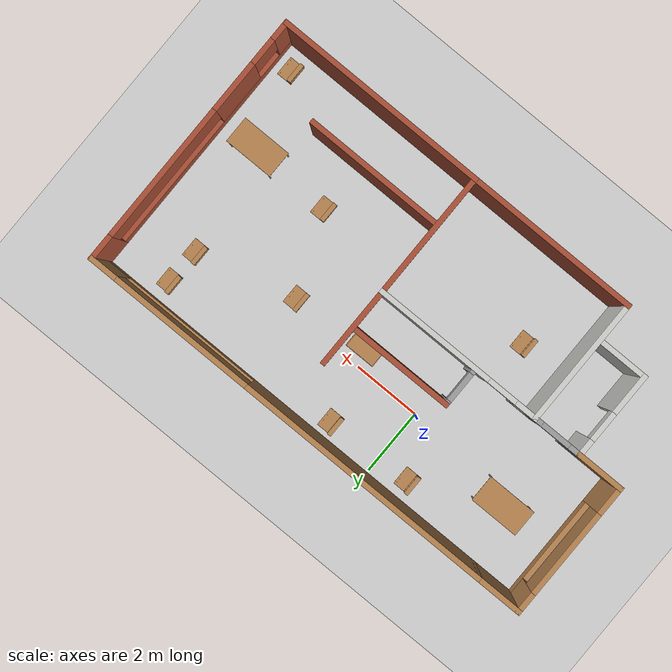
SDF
<sdf version="1.6">
 <world name="default">
  <plugin name="hello" filename="libhello.so"/>
  <light name="sun" type="directional">
   <pose>0 0 10 0 -0 0</pose>
   <diffuse>0.8 0.8 0.8 1</diffuse>
   <specular>0.2 0.2 0.2 1</specular>
   <attenuation>
    <range>1000</range>
    <constant>0.9</constant>
    <linear>0.01</linear>
    <quadratic>0.001</quadratic>
   </attenuation>
   <direction>-0.5 0.1 -0.9</direction>
  </light>
  <model name="ground_plane">
   <static>1</static>
   <link name="link">
    <collision name="collision">
     <geometry><plane><normal>0 0 1</normal><size>100 100</size></plane></geometry>
     <surface><friction><ode><mu>100</mu><mu2>50</mu2></ode></friction></surface>
    </collision>
    <visual name="visual">
     <cast_shadows>0</cast_shadows>
     <geometry><plane><normal>0 0 1</normal><size>100 100</size></plane></geometry>
     <material>
      <script><uri>file://media/materials/scripts/gazebo.material</uri><name>Gazebo/Grey</name></script>
     </material>
    </visual>
   </link>
  </model>
  <gravity>0 0 -9.8</gravity>
  <magnetic_field>6e-06 2.3e-05 -4.2e-05</magnetic_field>
  <atmosphere type="adiabatic"/>
  <physics name="default_physics" default="0" type="ode">
   <max_step_size>0.001</max_step_size>
   <real_time_factor>1</real_time_factor>
   <real_time_update_rate>1000</real_time_update_rate>
  </physics>
  <scene><ambient>0.4 0.4 0.4 1</ambient><background>0.7 0.7 0.7 1</background><shadows>1</shadows></scene>
  <spherical_coordinates>
   <surface_model>EARTH_WGS84</surface_model>
   <latitude_deg>0</latitude_deg>
   <longitude_deg>0</longitude_deg>
   <elevation>0</elevation>
   <heading_deg>0</heading_deg>
  </spherical_coordinates>
  <model name="myplace">
   <pose>1.99043 -1.78813 0 0 -0 0</pose>
   <link name="Wall_56">
    <pose>-5.02365 -0.175493 0 0 -0 3.14159</pose>
    <visual name="Wall_56_Visual_0">
     <pose>-0.660344 0 1.25 0 -0 0</pose>
     <geometry><box><size>0.30723 0.15 2.5</size></box></geometry>
     <material>
      <script><uri>file://media/materials/scripts/gazebo.material</uri><name>Gazebo/Grey</name></script>
      <ambient>1 1 1 1</ambient>
     </material>
     <meta><layer>0</layer></meta>
    </visual>
    <collision name="Wall_56_Collision_0">
     <geometry><box><size>0.30723 0.15 2.5</size></box></geometry>
     <pose>-0.660344 0 1.25 0 -0 0</pose>
    </collision>
    <visual name="Wall_56_Visual_1">
     <pose>0.603615 0 1.25 0 -0 0</pose>
     <geometry><box><size>0.420688 0.15 2.5</size></box></geometry>
     <material>
      <script><uri>file://media/materials/scripts/gazebo.material</uri><name>Gazebo/Grey</name></script>
      <ambient>1 1 1 1</ambient>
     </material>
     <meta><layer>0</layer></meta>
    </visual>
    <collision name="Wall_56_Collision_1">
     <geometry><box><size>0.420688 0.15 2.5</size></box></geometry>
     <pose>0.603615 0 1.25 0 -0 0</pose>
    </collision>
    <visual name="Wall_56_Visual_2">
     <pose>-0.056729 0 2.25 0 -0 0</pose>
     <geometry><box><size>0.9 0.15 0.5</size></box></geometry>
     <material>
      <script><uri>file://media/materials/scripts/gazebo.material</uri><name>Gazebo/Grey</name></script>
      <ambient>1 1 1 1</ambient>
     </material>
     <meta><layer>0</layer></meta>
    </visual>
    <collision name="Wall_56_Collision_2">
     <geometry><box><size>0.9 0.15 0.5</size></box></geometry>
     <pose>-0.056729 0 2.25 0 -0 0</pose>
    </collision>
   </link>
   <link name="Wall_58">
    <pose>0.66434 3.92507 0 0 -0 8.8e-05</pose>
    <visual name="Wall_58_Visual_0">
     <pose>-2.59963 0 1.25 0 -0 0</pose>
     <geometry><box><size>7.80465 0.15 2.5</size></box></geometry>
     <material>
      <script><uri>file://media/materials/scripts/gazebo.material</uri><name>Gazebo/Wood</name></script>
      <ambient>1 1 1 1</ambient>
     </material>
     <meta><layer>0</layer></meta>
    </visual>
    <collision name="Wall_58_Collision_0">
     <geometry><box><size>7.80465 0.15 2.5</size></box></geometry>
     <pose>-2.59963 0 1.25 0 -0 0</pose>
    </collision>
    <visual name="Wall_58_Visual_1">
     <pose>3.90232 0 0.25 0 -0 0</pose>
     <geometry><box><size>5.19925 0.15 0.5</size></box></geometry>
     <material>
      <script><uri>file://media/materials/scripts/gazebo.material</uri><name>Gazebo/Wood</name></script>
      <ambient>1 1 1 1</ambient>
     </material>
     <meta><layer>0</layer></meta>
    </visual>
    <collision name="Wall_58_Collision_1">
     <geometry><box><size>5.19925 0.15 0.5</size></box></geometry>
     <pose>3.90232 0 0.25 0 -0 0</pose>
    </collision>
    <visual name="Wall_58_Visual_2">
     <pose>6.07184 0 1.5 0 -0 0</pose>
     <geometry><box><size>0.860213 0.15 2</size></box></geometry>
     <material>
      <script><uri>file://media/materials/scripts/gazebo.material</uri><name>Gazebo/Wood</name></script>
      <ambient>1 1 1 1</ambient>
     </material>
     <meta><layer>0</layer></meta>
    </visual>
    <collision name="Wall_58_Collision_2">
     <geometry><box><size>0.860213 0.15 2</size></box></geometry>
     <pose>6.07184 0 1.5 0 -0 0</pose>
    </collision>
    <visual name="Wall_58_Visual_3">
     <pose>3.47222 0 1.9 0 -0 0</pose>
     <geometry><box><size>4.33904 0.15 1.2</size></box></geometry>
     <material>
      <script><uri>file://media/materials/scripts/gazebo.material</uri><name>Gazebo/Wood</name></script>
      <ambient>1 1 1 1</ambient>
     </material>
     <meta><layer>0</layer></meta>
    </visual>
    <collision name="Wall_58_Collision_3">
     <geometry><box><size>4.33904 0.15 1.2</size></box></geometry>
     <pose>3.47222 0 1.9 0 -0 0</pose>
    </collision>
   </link>
   <link name="Wall_59">
    <pose>7.11261 0.000633 0 0 0 -1.5708</pose>
    <visual name="Wall_59_Visual_0">
     <pose>-3.58058 0 1.25 0 -0 0</pose>
     <geometry><box><size>0.838846 0.15 2.5</size></box></geometry>
     <material>
      <script><uri>file://media/materials/scripts/gazebo.material</uri><name>Gazebo/Bricks</name></script>
      <ambient>1 1 1 1</ambient>
     </material>
     <meta><layer>0</layer></meta>
    </visual>
    <collision name="Wall_59_Collision_0">
     <geometry><box><size>0.838846 0.15 2.5</size></box></geometry>
     <pose>-3.58058 0 1.25 0 -0 0</pose>
    </collision>
    <visual name="Wall_59_Visual_1">
     <pose>0.419423 0 0.25 0 -0 0</pose>
     <geometry><box><size>7.16115 0.15 0.5</size></box></geometry>
     <material>
      <script><uri>file://media/materials/scripts/gazebo.material</uri><name>Gazebo/Bricks</name></script>
      <ambient>1 1 1 1</ambient>
     </material>
     <meta><layer>0</layer></meta>
    </visual>
    <collision name="Wall_59_Collision_1">
     <geometry><box><size>7.16115 0.15 0.5</size></box></geometry>
     <pose>0.419423 0 0.25 0 -0 0</pose>
    </collision>
    <visual name="Wall_59_Visual_2">
     <pose>1.80126 0 1.5 0 -0 0</pose>
     <geometry><box><size>1.54516 0.15 2</size></box></geometry>
     <material>
      <script><uri>file://media/materials/scripts/gazebo.material</uri><name>Gazebo/Bricks</name></script>
      <ambient>1 1 1 1</ambient>
     </material>
     <meta><layer>0</layer></meta>
    </visual>
    <collision name="Wall_59_Collision_2">
     <geometry><box><size>1.54516 0.15 2</size></box></geometry>
     <pose>1.80126 0 1.5 0 -0 0</pose>
    </collision>
    <visual name="Wall_59_Visual_3">
     <pose>3.68692 0 1.5 0 -0 0</pose>
     <geometry><box><size>0.62616 0.15 2</size></box></geometry>
     <material>
      <script><uri>file://media/materials/scripts/gazebo.material</uri><name>Gazebo/Bricks</name></script>
      <ambient>1 1 1 1</ambient>
     </material>
     <meta><layer>0</layer></meta>
    </visual>
    <collision name="Wall_59_Collision_3">
     <geometry><box><size>0.62616 0.15 2</size></box></geometry>
     <pose>3.68692 0 1.5 0 -0 0</pose>
    </collision>
    <visual name="Wall_59_Visual_4">
     <pose>-1.06624 0 1.9 0 -0 0</pose>
     <geometry><box><size>4.18983 0.15 1.2</size></box></geometry>
     <material>
      <script><uri>file://media/materials/scripts/gazebo.material</uri><name>Gazebo/Bricks</name></script>
      <ambient>1 1 1 1</ambient>
     </material>
     <meta><layer>0</layer></meta>
    </visual>
    <collision name="Wall_59_Collision_4">
     <geometry><box><size>4.18983 0.15 1.2</size></box></geometry>
     <pose>-1.06624 0 1.9 0 -0 0</pose>
    </collision>
    <visual name="Wall_59_Visual_5">
     <pose>2.97384 0 1.9 0 -0 0</pose>
     <geometry><box><size>0.8 0.15 1.2</size></box></geometry>
     <material>
      <script><uri>file://media/materials/scripts/gazebo.material</uri><name>Gazebo/Bricks</name></script>
      <ambient>1 1 1 1</ambient>
     </material>
     <meta><layer>0</layer></meta>
    </visual>
    <collision name="Wall_59_Collision_5">
     <geometry><box><size>0.8 0.15 1.2</size></box></geometry>
     <pose>2.97384 0 1.9 0 -0 0</pose>
    </collision>
   </link>
   <link name="Wall_60">
    <collision name="Wall_60_Collision">
     <geometry><box><size>6.41862 0.15 2.5</size></box></geometry>
     <pose>0 0 1.25 0 -0 0</pose>
    </collision>
    <visual name="Wall_60_Visual">
     <pose>0 0 1.25 0 -0 0</pose>
     <geometry><box><size>6.41862 0.15 2.5</size></box></geometry>
     <material>
      <script><uri>file://media/materials/scripts/gazebo.material</uri><name>Gazebo/Bricks</name></script>
      <ambient>1 1 1 1</ambient>
     </material>
     <meta><layer>0</layer></meta>
    </visual>
    <pose>3.95698 -3.92493 0 0 0 -3.14141</pose>
   </link>
   <link name="Wall_69">
    <pose>-1.73469 -0.175493 0 0 -0 0</pose>
    <visual name="Wall_69_Visual_0">
     <pose>-2.26885 0 1.25 0 -0 0</pose>
     <geometry><box><size>0.712304 0.15 2.5</size></box></geometry>
     <material>
      <script><uri>file://media/materials/scripts/gazebo.material</uri><name>Gazebo/CeilingTiled</name></script>
      <ambient>1 1 1 1</ambient>
     </material>
     <meta><layer>0</layer></meta>
    </visual>
    <collision name="Wall_69_Collision_0">
     <geometry><box><size>0.712304 0.15 2.5</size></box></geometry>
     <pose>-2.26885 0 1.25 0 -0 0</pose>
    </collision>
    <visual name="Wall_69_Visual_1">
     <pose>0.806152 0 1.25 0 -0 0</pose>
     <geometry><box><size>3.6377 0.15 2.5</size></box></geometry>
     <material>
      <script><uri>file://media/materials/scripts/gazebo.material</uri><name>Gazebo/CeilingTiled</name></script>
      <ambient>1 1 1 1</ambient>
     </material>
     <meta><layer>0</layer></meta>
    </visual>
    <collision name="Wall_69_Collision_1">
     <geometry><box><size>3.6377 0.15 2.5</size></box></geometry>
     <pose>0.806152 0 1.25 0 -0 0</pose>
    </collision>
    <visual name="Wall_69_Visual_2">
     <pose>-1.4627 0 2.25 0 -0 0</pose>
     <geometry><box><size>0.9 0.15 0.5</size></box></geometry>
     <material>
      <script><uri>file://media/materials/scripts/gazebo.material</uri><name>Gazebo/CeilingTiled</name></script>
      <ambient>1 1 1 1</ambient>
     </material>
     <meta><layer>0</layer></meta>
    </visual>
    <collision name="Wall_69_Collision_2">
     <geometry><box><size>0.9 0.15 0.5</size></box></geometry>
     <pose>-1.4627 0 2.25 0 -0 0</pose>
    </collision>
   </link>
   <link name="Wall_72">
    <collision name="Wall_72_Collision">
     <geometry><box><size>3.90001 0.15 2.5</size></box></geometry>
     <pose>0 0 1.25 0 -0 0</pose>
    </collision>
    <visual name="Wall_72_Visual">
     <pose>0 0 1.25 0 -0 0</pose>
     <geometry><box><size>3.90001 0.15 2.5</size></box></geometry>
     <material>
      <script><uri>file://media/materials/scripts/gazebo.material</uri><name>Gazebo/Bricks</name></script>
      <ambient>1 1 1 1</ambient>
     </material>
     <meta><layer>0</layer></meta>
    </visual>
    <pose>0.818989 -2.05049 0 0 0 -1.56883</pose>
   </link>
   <link name="Wall_74">
    <collision name="Wall_74_Collision">
     <geometry><box><size>5.25 0.15 2.5</size></box></geometry>
     <pose>0 0 1.25 0 -0 0</pose>
    </collision>
    <visual name="Wall_74_Visual">
     <pose>0 0 1.25 0 -0 0</pose>
     <geometry><box><size>5.25 0.15 2.5</size></box></geometry>
     <material>
      <script><uri>file://media/materials/scripts/gazebo.material</uri><name>Gazebo/Bricks</name></script>
      <ambient>1 1 1 1</ambient>
     </material>
     <meta><layer>0</layer></meta>
    </visual>
    <pose>-1.72733 -3.92549 0 0 -0 3.14159</pose>
   </link>
   <link name="Wall_75">
    <collision name="Wall_75_Collision">
     <geometry><box><size>3.90001 0.15 2.5</size></box></geometry>
     <pose>0 0 1.25 0 -0 0</pose>
    </collision>
    <visual name="Wall_75_Visual">
     <pose>0 0 1.25 0 -0 0</pose>
     <geometry><box><size>3.90001 0.15 2.5</size></box></geometry>
     <material>
      <script><uri>file://media/materials/scripts/gazebo.material</uri><name>Gazebo/CeilingTiled</name></script>
      <ambient>1 1 1 1</ambient>
     </material>
     <meta><layer>0</layer></meta>
    </visual>
    <pose>-4.28101 -2.05049 0 0 -0 1.57276</pose>
   </link>
   <link name="Wall_79">
    <collision name="Wall_79_Collision">
     <geometry><box><size>2.5 0.15 2.5</size></box></geometry>
     <pose>0 0 1.25 0 -0 0</pose>
    </collision>
    <visual name="Wall_79_Visual">
     <pose>0 0 1.25 0 -0 0</pose>
     <geometry><box><size>2.5 0.15 2.5</size></box></geometry>
     <material>
      <script><uri>file://media/materials/scripts/gazebo.material</uri><name>Gazebo/Bricks</name></script>
      <ambient>1 1 1 1</ambient>
     </material>
     <meta><layer>0</layer></meta>
    </visual>
    <pose>0.815308 0.999507 0 0 -0 1.5708</pose>
   </link>
   <link name="Wall_81">
    <collision name="Wall_81_Collision">
     <geometry><box><size>4.25 0.15 2.5</size></box></geometry>
     <pose>0 0 1.25 0 -0 0</pose>
    </collision>
    <visual name="Wall_81_Visual">
     <pose>0 0 1.25 0 -0 0</pose>
     <geometry><box><size>4.25 0.15 2.5</size></box></geometry>
     <material>
      <script><uri>file://media/materials/scripts/gazebo.material</uri><name>Gazebo/Bricks</name></script>
      <ambient>1 1 1 1</ambient>
     </material>
     <meta><layer>0</layer></meta>
    </visual>
    <pose>2.90335 -2.39757 0 0 -0 0</pose>
   </link>
   <link name="Wall_83">
    <collision name="Wall_83_Collision">
     <geometry><box><size>3.25 0.15 2.5</size></box></geometry>
     <pose>0 0 1.25 0 -0 0</pose>
    </collision>
    <visual name="Wall_83_Visual">
     <pose>0 0 1.25 0 -0 0</pose>
     <geometry><box><size>3.25 0.15 2.5</size></box></geometry>
     <material>
      <script><uri>file://media/materials/scripts/gazebo.material</uri><name>Gazebo/Bricks</name></script>
      <ambient>1 1 1 1</ambient>
     </material>
     <meta><layer>0</layer></meta>
    </visual>
    <pose>-0.739288 1.01357 0 0 -0 3.14159</pose>
   </link>
   <link name="Wall_84">
    <pose>-2.28929 0.463574 0 0 0 -1.5708</pose>
    <visual name="Wall_84_Visual_0">
     <pose>-0.524684 0 1.25 0 -0 0</pose>
     <geometry><box><size>0.200631 0.15 2.5</size></box></geometry>
     <material>
      <script><uri>file://media/materials/scripts/gazebo.material</uri><name>Gazebo/Grey</name></script>
      <ambient>1 1 1 1</ambient>
     </material>
     <meta><layer>0</layer></meta>
    </visual>
    <collision name="Wall_84_Collision_0">
     <geometry><box><size>0.200631 0.15 2.5</size></box></geometry>
     <pose>-0.524684 0 1.25 0 -0 0</pose>
    </collision>
    <visual name="Wall_84_Visual_1">
     <pose>0.550316 0 1.25 0 -0 0</pose>
     <geometry><box><size>0.149369 0.15 2.5</size></box></geometry>
     <material>
      <script><uri>file://media/materials/scripts/gazebo.material</uri><name>Gazebo/Grey</name></script>
      <ambient>1 1 1 1</ambient>
     </material>
     <meta><layer>0</layer></meta>
    </visual>
    <collision name="Wall_84_Collision_1">
     <geometry><box><size>0.149369 0.15 2.5</size></box></geometry>
     <pose>0.550316 0 1.25 0 -0 0</pose>
    </collision>
    <visual name="Wall_84_Visual_2">
     <pose>0.025631 0 2.25 0 -0 0</pose>
     <geometry><box><size>0.9 0.15 0.5</size></box></geometry>
     <material>
      <script><uri>file://media/materials/scripts/gazebo.material</uri><name>Gazebo/Grey</name></script>
      <ambient>1 1 1 1</ambient>
     </material>
     <meta><layer>0</layer></meta>
    </visual>
    <collision name="Wall_84_Collision_2">
     <geometry><box><size>0.9 0.15 0.5</size></box></geometry>
     <pose>0.025631 0 2.25 0 -0 0</pose>
    </collision>
   </link>
   <link name="Wall_86">
    <pose>-5.76261 -1.47549 0 0 0 -1.5708</pose>
    <visual name="Wall_86_Visual_0">
     <pose>-1.09105 0 1.25 0 -0 0</pose>
     <geometry><box><size>0.567901 0.15 2.5</size></box></geometry>
     <material>
      <script><uri>file://media/materials/scripts/gazebo.material</uri><name>Gazebo/CeilingTiled</name></script>
      <ambient>1 1 1 1</ambient>
     </material>
     <meta><layer>0</layer></meta>
    </visual>
    <collision name="Wall_86_Collision_0">
     <geometry><box><size>0.567901 0.15 2.5</size></box></geometry>
     <pose>-1.09105 0 1.25 0 -0 0</pose>
    </collision>
    <visual name="Wall_86_Visual_1">
     <pose>0.73395 0 1.25 0 -0 0</pose>
     <geometry><box><size>1.2821 0.15 2.5</size></box></geometry>
     <material>
      <script><uri>file://media/materials/scripts/gazebo.material</uri><name>Gazebo/CeilingTiled</name></script>
      <ambient>1 1 1 1</ambient>
     </material>
     <meta><layer>0</layer></meta>
    </visual>
    <collision name="Wall_86_Collision_1">
     <geometry><box><size>1.2821 0.15 2.5</size></box></geometry>
     <pose>0.73395 0 1.25 0 -0 0</pose>
    </collision>
    <visual name="Wall_86_Visual_2">
     <pose>-0.357099 0 2.25 0 -0 0</pose>
     <geometry><box><size>0.9 0.15 0.5</size></box></geometry>
     <material>
      <script><uri>file://media/materials/scripts/gazebo.material</uri><name>Gazebo/CeilingTiled</name></script>
      <ambient>1 1 1 1</ambient>
     </material>
     <meta><layer>0</layer></meta>
    </visual>
    <collision name="Wall_86_Collision_2">
     <geometry><box><size>0.9 0.15 0.5</size></box></geometry>
     <pose>-0.357099 0 2.25 0 -0 0</pose>
    </collision>
   </link>
   <link name="Wall_87">
    <collision name="Wall_87_Collision">
     <geometry><box><size>1.5 0.15 2.5</size></box></geometry>
     <pose>0 0 1.25 0 -0 0</pose>
    </collision>
    <visual name="Wall_87_Visual">
     <pose>0 0 1.25 0 -0 0</pose>
     <geometry><box><size>1.5 0.15 2.5</size></box></geometry>
     <material>
      <script><uri>file://media/materials/scripts/gazebo.material</uri><name>Gazebo/CeilingTiled</name></script>
      <ambient>1 1 1 1</ambient>
     </material>
     <meta><layer>0</layer></meta>
    </visual>
    <pose>-5.08761 -2.77549 0 0 -0 0</pose>
   </link>
   <link name="Wall_89">
    <collision name="Wall_89_Collision">
     <geometry><box><size>1.5 0.15 2.5</size></box></geometry>
     <pose>0 0 1.25 0 -0 0</pose>
    </collision>
    <visual name="Wall_89_Visual">
     <pose>0 0 1.25 0 -0 0</pose>
     <geometry><box><size>1.5 0.15 2.5</size></box></geometry>
     <material>
      <script><uri>file://media/materials/scripts/gazebo.material</uri><name>Gazebo/Wood</name></script>
      <ambient>1 1 1 1</ambient>
     </material>
     <meta><layer>0</layer></meta>
    </visual>
    <pose>-6.43761 -0.175493 0 0 -0 3.14159</pose>
   </link>
   <link name="Wall_90">
    <pose>-7.11261 1.87451 0 0 -0 1.5708</pose>
    <visual name="Wall_90_Visual_0">
     <pose>-1.66099 0 1.25 0 -0 0</pose>
     <geometry><box><size>0.928026 0.15 2.5</size></box></geometry>
     <material>
      <script><uri>file://media/materials/scripts/gazebo.material</uri><name>Gazebo/Wood</name></script>
      <ambient>1 1 1 1</ambient>
     </material>
     <meta><layer>0</layer></meta>
    </visual>
    <collision name="Wall_90_Collision_0">
     <geometry><box><size>0.928026 0.15 2.5</size></box></geometry>
     <pose>-1.66099 0 1.25 0 -0 0</pose>
    </collision>
    <visual name="Wall_90_Visual_1">
     <pose>0.464013 0 0.25 0 -0 0</pose>
     <geometry><box><size>3.32197 0.15 0.5</size></box></geometry>
     <material>
      <script><uri>file://media/materials/scripts/gazebo.material</uri><name>Gazebo/Wood</name></script>
      <ambient>1 1 1 1</ambient>
     </material>
     <meta><layer>0</layer></meta>
    </visual>
    <collision name="Wall_90_Collision_1">
     <geometry><box><size>3.32197 0.15 0.5</size></box></geometry>
     <pose>0.464013 0 0.25 0 -0 0</pose>
    </collision>
    <visual name="Wall_90_Visual_2">
     <pose>1.79142 0 1.5 0 -0 0</pose>
     <geometry><box><size>0.667162 0.15 2</size></box></geometry>
     <material>
      <script><uri>file://media/materials/scripts/gazebo.material</uri><name>Gazebo/Wood</name></script>
      <ambient>1 1 1 1</ambient>
     </material>
     <meta><layer>0</layer></meta>
    </visual>
    <collision name="Wall_90_Collision_2">
     <geometry><box><size>0.667162 0.15 2</size></box></geometry>
     <pose>1.79142 0 1.5 0 -0 0</pose>
    </collision>
    <visual name="Wall_90_Visual_3">
     <pose>0.130432 0 1.9 0 -0 0</pose>
     <geometry><box><size>2.65481 0.15 1.2</size></box></geometry>
     <material>
      <script><uri>file://media/materials/scripts/gazebo.material</uri><name>Gazebo/Wood</name></script>
      <ambient>1 1 1 1</ambient>
     </material>
     <meta><layer>0</layer></meta>
    </visual>
    <collision name="Wall_90_Collision_3">
     <geometry><box><size>2.65481 0.15 1.2</size></box></geometry>
     <pose>0.130432 0 1.9 0 -0 0</pose>
    </collision>
   </link>
   <link name="Wall_91">
    <collision name="Wall_91_Collision">
     <geometry><box><size>1.5 0.15 2.5</size></box></geometry>
     <pose>0 0 1.25 0 -0 0</pose>
    </collision>
    <visual name="Wall_91_Visual">
     <pose>0 0 1.25 0 -0 0</pose>
     <geometry><box><size>1.5 0.15 2.5</size></box></geometry>
     <material>
      <script><uri>file://media/materials/scripts/gazebo.material</uri><name>Gazebo/Wood</name></script>
      <ambient>1 1 1 1</ambient>
     </material>
     <meta><layer>0</layer></meta>
    </visual>
    <pose>-6.43761 3.92451 0 0 -0 0</pose>
   </link>
   <static>1</static>
  </model>
  <model name="table">
   <static>1</static>
   <link name="link">
    <collision name="surface">
     <pose>0 0 1 0 -0 0</pose>
     <geometry><box><size>1.5 0.8 0.03</size></box></geometry>
     <surface><friction><ode><mu>0.6</mu><mu2>0.6</mu2></ode></friction></surface>
    </collision>
    <visual name="visual1">
     <pose>0 0 1 0 -0 0</pose>
     <geometry><box><size>1.5 0.8 0.03</size></box></geometry>
     <material>
      <script><uri>file://media/materials/scripts/gazebo.material</uri><name>Gazebo/Wood</name></script>
     </material>
    </visual>
    <collision name="front_left_leg">
     <pose>0.68 0.38 0.5 0 -0 0</pose>
     <geometry><cylinder><radius>0.02</radius><length>1</length></cylinder></geometry>
    </collision>
    <visual name="front_left_leg">
     <pose>0.68 0.38 0.5 0 -0 0</pose>
     <geometry><cylinder><radius>0.02</radius><length>1</length></cylinder></geometry>
     <material>
      <script><uri>file://media/materials/scripts/gazebo.material</uri><name>Gazebo/Grey</name></script>
     </material>
    </visual>
    <collision name="front_right_leg">
     <pose>0.68 -0.38 0.5 0 -0 0</pose>
     <geometry><cylinder><radius>0.02</radius><length>1</length></cylinder></geometry>
    </collision>
    <visual name="front_right_leg">
     <pose>0.68 -0.38 0.5 0 -0 0</pose>
     <geometry><cylinder><radius>0.02</radius><length>1</length></cylinder></geometry>
     <material>
      <script><uri>file://media/materials/scripts/gazebo.material</uri><name>Gazebo/Grey</name></script>
     </material>
    </visual>
    <collision name="back_right_leg">
     <pose>-0.68 -0.38 0.5 0 -0 0</pose>
     <geometry><cylinder><radius>0.02</radius><length>1</length></cylinder></geometry>
    </collision>
    <visual name="back_right_leg">
     <pose>-0.68 -0.38 0.5 0 -0 0</pose>
     <geometry><cylinder><radius>0.02</radius><length>1</length></cylinder></geometry>
     <material>
      <script><uri>file://media/materials/scripts/gazebo.material</uri><name>Gazebo/Grey</name></script>
     </material>
    </visual>
    <collision name="back_left_leg">
     <pose>-0.68 0.38 0.5 0 -0 0</pose>
     <geometry><cylinder><radius>0.02</radius><length>1</length></cylinder></geometry>
    </collision>
    <visual name="back_left_leg">
     <pose>-0.68 0.38 0.5 0 -0 0</pose>
     <geometry><cylinder><radius>0.02</radius><length>1</length></cylinder></geometry>
     <material>
      <script><uri>file://media/materials/scripts/gazebo.material</uri><name>Gazebo/Grey</name></script>
     </material>
    </visual>
   </link>
   <pose>-3.31314 0.360386 0 0 -0 0</pose>
  </model>
  <model name="bookshelf">
   <static>1</static>
   <link name="link">
    <inertial><mass>1</mass></inertial>
    <collision name="back">
     <pose>0 0.005 0.6 0 -0 0</pose>
     <geometry><box><size>0.9 0.01 1.2</size></box></geometry>
    </collision>
    <visual name="visual1">
     <pose>0 0.005 0.6 0 -0 0</pose>
     <geometry><box><size>0.9 0.01 1.2</size></box></geometry>
     <material>
      <script><uri>file://media/materials/scripts/gazebo.material</uri><name>Gazebo/Wood</name></script>
     </material>
    </visual>
    <collision name="left_side">
     <pose>0.45 -0.195 0.6 0 -0 0</pose>
     <geometry><box><size>0.02 0.4 1.2</size></box></geometry>
    </collision>
    <visual name="visual2">
     <pose>0.45 -0.195 0.6 0 -0 0</pose>
     <geometry><box><size>0.02 0.4 1.2</size></box></geometry>
     <material>
      <script><uri>file://media/materials/scripts/gazebo.material</uri><name>Gazebo/Wood</name></script>
     </material>
    </visual>
    <collision name="right_side">
     <pose>-0.45 -0.195 0.6 0 -0 0</pose>
     <geometry><box><size>0.02 0.4 1.2</size></box></geometry>
    </collision>
    <visual name="visual3">
     <pose>-0.45 -0.195 0.6 0 -0 0</pose>
     <geometry><box><size>0.02 0.4 1.2</size></box></geometry>
     <material>
      <script><uri>file://media/materials/scripts/gazebo.material</uri><name>Gazebo/Wood</name></script>
     </material>
    </visual>
    <collision name="bottom">
     <pose>0 -0.195 0.03 0 -0 0</pose>
     <geometry><box><size>0.88 0.4 0.06</size></box></geometry>
    </collision>
    <visual name="visual4">
     <pose>0 -0.195 0.03 0 -0 0</pose>
     <geometry><box><size>0.88 0.4 0.06</size></box></geometry>
     <material>
      <script><uri>file://media/materials/scripts/gazebo.material</uri><name>Gazebo/Wood</name></script>
     </material>
    </visual>
    <collision name="top">
     <pose>0 -0.195 1.19 0 -0 0</pose>
     <geometry><box><size>0.88 0.4 0.02</size></box></geometry>
    </collision>
    <visual name="visual5">
     <pose>0 -0.195 1.19 0 -0 0</pose>
     <geometry><box><size>0.88 0.4 0.02</size></box></geometry>
     <material>
      <script><uri>file://media/materials/scripts/gazebo.material</uri><name>Gazebo/Wood</name></script>
     </material>
    </visual>
    <collision name="low_shelf">
     <pose>0 -0.195 0.43 0 -0 0</pose>
     <geometry><box><size>0.88 0.4 0.02</size></box></geometry>
    </collision>
    <visual name="visual6">
     <pose>0 -0.195 0.43 0 -0 0</pose>
     <geometry><box><size>0.88 0.4 0.02</size></box></geometry>
     <material>
      <script><uri>file://media/materials/scripts/gazebo.material</uri><name>Gazebo/Wood</name></script>
     </material>
    </visual>
    <collision name="high_shelf">
     <pose>0 -0.195 0.8 0 -0 0</pose>
     <geometry><box><size>0.88 0.4 0.02</size></box></geometry>
    </collision>
    <visual name="visual7">
     <pose>0 -0.195 0.8 0 -0 0</pose>
     <geometry><box><size>0.88 0.4 0.02</size></box></geometry>
     <material>
      <script><uri>file://media/materials/scripts/gazebo.material</uri><name>Gazebo/Wood</name></script>
     </material>
    </visual>
   </link>
   <pose>2.20301 -0.290207 0 0 -0 0</pose>
  </model>
  <model name="wooden_case">
   <link name="base">
    <pose>0 0 0.024 0 -0 0</pose>
    <inertial>
     <pose>-0.022184 0 0.171592 0 -0 0</pose>
     <mass>3.96264</mass>
     <inertia>
      <ixx>0.213536</ixx>
      <ixy>0</ixy>
      <ixz>0.000779377</ixz>
      <iyy>0.0708943</iyy>
      <iyz>0</iyz>
      <izz>0.154604</izz>
     </inertia>
    </inertial>
    <collision name="collision_back">
     <pose>-0.053975 0 0.1778 0 -0 0</pose>
     <geometry><box><size>0.01905 0.5461 0.3175</size></box></geometry>
     <surface>
      <contact>
       <poissons_ratio>0.347</poissons_ratio>
       <elastic_modulus>8.8e+09</elastic_modulus>
       <ode><kp>100000</kp><kd>100</kd><max_vel>100</max_vel><min_depth>0.001</min_depth></ode>
      </contact>
      <friction>
       <torsional>
        <coefficient>1</coefficient>
        <use_patch_radius>0</use_patch_radius>
        <surface_radius>0.01</surface_radius>
       </torsional>
      </friction>
     </surface>
    </collision>
    <visual name="visual_back">
     <pose>-0.053975 0 0.1778 0 -0 0</pose>
     <geometry><box><size>0.01905 0.5461 0.3175</size></box></geometry>
     <material>
      <script><uri>file://media/materials/scripts/gazebo.material</uri><name>Gazebo/Wood</name></script>
     </material>
    </visual>
    <collision name="collision_bottom">
     <pose>0 0 0.009525 0 -0 0</pose>
     <geometry><box><size>0.127 0.5842 0.01905</size></box></geometry>
     <surface>
      <contact>
       <poissons_ratio>0.347</poissons_ratio>
       <elastic_modulus>8.8e+09</elastic_modulus>
       <ode><kp>100000</kp><kd>100</kd><max_vel>100</max_vel><min_depth>0.001</min_depth></ode>
      </contact>
      <friction>
       <torsional>
        <coefficient>1</coefficient>
        <use_patch_radius>0</use_patch_radius>
        <surface_radius>0.01</surface_radius>
       </torsional>
      </friction>
     </surface>
    </collision>
    <visual name="visual_bottom">
     <pose>0 0 0.009525 0 -0 0</pose>
     <geometry><box><size>0.127 0.5842 0.01905</size></box></geometry>
     <material>
      <script><uri>file://media/materials/scripts/gazebo.material</uri><name>Gazebo/Wood</name></script>
     </material>
    </visual>
    <collision name="collision_top">
     <pose>0 0 0.346075 0 -0 0</pose>
     <geometry><box><size>0.127 0.5842 0.01905</size></box></geometry>
     <surface>
      <contact>
       <poissons_ratio>0.347</poissons_ratio>
       <elastic_modulus>8.8e+09</elastic_modulus>
       <ode><kp>100000</kp><kd>100</kd><max_vel>100</max_vel><min_depth>0.001</min_depth></ode>
      </contact>
      <friction>
       <torsional>
        <coefficient>1</coefficient>
        <use_patch_radius>0</use_patch_radius>
        <surface_radius>0.01</surface_radius>
       </torsional>
      </friction>
     </surface>
    </collision>
    <visual name="visual_top">
     <pose>0 0 0.346075 0 -0 0</pose>
     <geometry><box><size>0.127 0.5842 0.01905</size></box></geometry>
     <material>
      <script><uri>file://media/materials/scripts/gazebo.material</uri><name>Gazebo/Wood</name></script>
     </material>
    </visual>
    <collision name="collision_left">
     <pose>0 -0.282575 0.1778 0 -0 0</pose>
     <geometry><box><size>0.127 0.01905 0.3175</size></box></geometry>
     <surface>
      <contact>
       <poissons_ratio>0.347</poissons_ratio>
       <elastic_modulus>8.8e+09</elastic_modulus>
       <ode><kp>100000</kp><kd>100</kd><max_vel>100</max_vel><min_depth>0.001</min_depth></ode>
      </contact>
      <friction>
       <torsional>
        <coefficient>1</coefficient>
        <use_patch_radius>0</use_patch_radius>
        <surface_radius>0.01</surface_radius>
       </torsional>
      </friction>
     </surface>
    </collision>
    <visual name="visual_left">
     <pose>0 -0.282575 0.1778 0 -0 0</pose>
     <geometry><box><size>0.127 0.01905 0.3175</size></box></geometry>
     <material>
      <script><uri>file://media/materials/scripts/gazebo.material</uri><name>Gazebo/Wood</name></script>
     </material>
    </visual>
    <collision name="collision_right">
     <pose>0 0.282575 0.1778 0 -0 0</pose>
     <geometry><box><size>0.127 0.01905 0.3175</size></box></geometry>
     <surface>
      <contact>
       <poissons_ratio>0.347</poissons_ratio>
       <elastic_modulus>8.8e+09</elastic_modulus>
       <ode><kp>100000</kp><kd>100</kd><max_vel>100</max_vel><min_depth>0.001</min_depth></ode>
      </contact>
      <friction>
       <torsional>
        <coefficient>1</coefficient>
        <use_patch_radius>0</use_patch_radius>
        <surface_radius>0.01</surface_radius>
       </torsional>
      </friction>
     </surface>
    </collision>
    <visual name="visual_right">
     <pose>0 0.282575 0.1778 0 -0 0</pose>
     <geometry><box><size>0.127 0.01905 0.3175</size></box></geometry>
     <material>
      <script><uri>file://media/materials/scripts/gazebo.material</uri><name>Gazebo/Wood</name></script>
     </material>
    </visual>
    <collision name="collision_block_left">
     <pose>0.0095 -0.2151 -0.012 0 -0 0</pose>
     <geometry><box><size>0.108 0.05 0.024</size></box></geometry>
     <surface>
      <contact>
       <poissons_ratio>0.347</poissons_ratio>
       <elastic_modulus>8.8e+09</elastic_modulus>
       <ode><kp>100000</kp><kd>100</kd><max_vel>100</max_vel><min_depth>0.001</min_depth></ode>
      </contact>
      <friction>
       <torsional>
        <coefficient>1</coefficient>
        <use_patch_radius>0</use_patch_radius>
        <surface_radius>0.01</surface_radius>
       </torsional>
      </friction>
     </surface>
    </collision>
    <visual name="visual_block_left">
     <pose>0.0095 -0.2151 -0.012 0 -0 0</pose>
     <geometry><box><size>0.108 0.05 0.024</size></box></geometry>
     <material>
      <script><uri>file://media/materials/scripts/gazebo.material</uri><name>Gazebo/Wood</name></script>
     </material>
    </visual>
    <collision name="collision_block_right">
     <pose>0.0095 0.2151 -0.012 0 -0 0</pose>
     <geometry><box><size>0.108 0.05 0.024</size></box></geometry>
     <surface>
      <contact>
       <poissons_ratio>0.347</poissons_ratio>
       <elastic_modulus>8.8e+09</elastic_modulus>
       <ode><kp>100000</kp><kd>100</kd><max_vel>100</max_vel><min_depth>0.001</min_depth></ode>
      </contact>
      <friction>
       <torsional>
        <coefficient>1</coefficient>
        <use_patch_radius>0</use_patch_radius>
        <surface_radius>0.01</surface_radius>
       </torsional>
      </friction>
     </surface>
    </collision>
    <visual name="visual_block_right">
     <pose>0.0095 0.2151 -0.012 0 -0 0</pose>
     <geometry><box><size>0.108 0.05 0.024</size></box></geometry>
     <material>
      <script><uri>file://media/materials/scripts/gazebo.material</uri><name>Gazebo/Wood</name></script>
     </material>
    </visual>
   </link>
   <link name="lid">
    <pose>0.243775 0 0.009525 0 -0 0</pose>
    <inertial>
     <mass>1.97874</mass>
     <inertia>
      <ixx>0.0563367</ixx>
      <ixy>0</ixy>
      <ixz>0</ixz>
      <iyy>0.020911</iyy>
      <iyz>0</iyz>
      <izz>0.0771281</izz>
     </inertia>
    </inertial>
    <collision name="collision">
     <geometry><box><size>0.3556 0.5842 0.01905</size></box></geometry>
     <surface>
      <contact>
       <poissons_ratio>0.347</poissons_ratio>
       <elastic_modulus>8.8e+09</elastic_modulus>
       <ode><kp>100000</kp><kd>100</kd><max_vel>100</max_vel><min_depth>0.001</min_depth></ode>
      </contact>
      <friction>
       <torsional>
        <coefficient>1</coefficient>
        <use_patch_radius>0</use_patch_radius>
        <surface_radius>0.01</surface_radius>
       </torsional>
      </friction>
     </surface>
    </collision>
    <visual name="visual">
     <geometry><box><size>0.3556 0.5842 0.01905</size></box></geometry>
     <material>
      <script><uri>file://media/materials/scripts/gazebo.material</uri><name>Gazebo/Wood</name></script>
     </material>
    </visual>
    <visual name="tee_nut_1">
     <pose>0.122 -0.216 0 0 -0 0</pose>
     <geometry><cylinder><radius>0.00635</radius><length>0.0192405</length></cylinder></geometry>
     <material>
      <script><uri>file://media/materials/scripts/gazebo.material</uri><name>Gazebo/Grey</name></script>
     </material>
    </visual>
    <visual name="tee_nut_2">
     <pose>0.122 -0.088 0 0 -0 0</pose>
     <geometry><cylinder><radius>0.00635</radius><length>0.0192405</length></cylinder></geometry>
     <material>
      <script><uri>file://media/materials/scripts/gazebo.material</uri><name>Gazebo/Grey</name></script>
     </material>
    </visual>
    <visual name="tee_nut_3">
     <pose>0.122 0.088 0 0 -0 0</pose>
     <geometry><cylinder><radius>0.00635</radius><length>0.0192405</length></cylinder></geometry>
     <material>
      <script><uri>file://media/materials/scripts/gazebo.material</uri><name>Gazebo/Grey</name></script>
     </material>
    </visual>
    <visual name="tee_nut_4">
     <pose>0.122 0.216 0 0 -0 0</pose>
     <geometry><cylinder><radius>0.00635</radius><length>0.0192405</length></cylinder></geometry>
     <material>
      <script><uri>file://media/materials/scripts/gazebo.material</uri><name>Gazebo/Grey</name></script>
     </material>
    </visual>
   </link>
   <joint name="lid_hinge" type="revolute">
    <pose>-0.1778 0 0.01905 0 -0 0</pose>
    <parent>base</parent>
    <child>lid</child>
    <axis>
     <xyz>0 1 0</xyz>
     <limit><upper>0.523599</upper><lower>-1.5708</lower></limit>
     <use_parent_model_frame>0</use_parent_model_frame>
     <dynamics><spring_reference>0</spring_reference><spring_stiffness>0</spring_stiffness></dynamics>
    </axis>
   </joint>
   <pose>7.31042 1.46622 -0.001057 0 -0.000429 0</pose>
  </model>
  <model name="wooden_case_0">
   <link name="base">
    <pose>0 0 0.024 0 -0 0</pose>
    <inertial>
     <pose>-0.022184 0 0.171592 0 -0 0</pose>
     <mass>3.96264</mass>
     <inertia>
      <ixx>0.213536</ixx>
      <ixy>0</ixy>
      <ixz>0.000779377</ixz>
      <iyy>0.0708943</iyy>
      <iyz>0</iyz>
      <izz>0.154604</izz>
     </inertia>
    </inertial>
    <collision name="collision_back">
     <pose>-0.053975 0 0.1778 0 -0 0</pose>
     <geometry><box><size>0.01905 0.5461 0.3175</size></box></geometry>
     <surface>
      <contact>
       <poissons_ratio>0.347</poissons_ratio>
       <elastic_modulus>8.8e+09</elastic_modulus>
       <ode><kp>100000</kp><kd>100</kd><max_vel>100</max_vel><min_depth>0.001</min_depth></ode>
      </contact>
      <friction>
       <torsional>
        <coefficient>1</coefficient>
        <use_patch_radius>0</use_patch_radius>
        <surface_radius>0.01</surface_radius>
       </torsional>
      </friction>
     </surface>
    </collision>
    <visual name="visual_back">
     <pose>-0.053975 0 0.1778 0 -0 0</pose>
     <geometry><box><size>0.01905 0.5461 0.3175</size></box></geometry>
     <material>
      <script><uri>file://media/materials/scripts/gazebo.material</uri><name>Gazebo/Wood</name></script>
     </material>
    </visual>
    <collision name="collision_bottom">
     <pose>0 0 0.009525 0 -0 0</pose>
     <geometry><box><size>0.127 0.5842 0.01905</size></box></geometry>
     <surface>
      <contact>
       <poissons_ratio>0.347</poissons_ratio>
       <elastic_modulus>8.8e+09</elastic_modulus>
       <ode><kp>100000</kp><kd>100</kd><max_vel>100</max_vel><min_depth>0.001</min_depth></ode>
      </contact>
      <friction>
       <torsional>
        <coefficient>1</coefficient>
        <use_patch_radius>0</use_patch_radius>
        <surface_radius>0.01</surface_radius>
       </torsional>
      </friction>
     </surface>
    </collision>
    <visual name="visual_bottom">
     <pose>0 0 0.009525 0 -0 0</pose>
     <geometry><box><size>0.127 0.5842 0.01905</size></box></geometry>
     <material>
      <script><uri>file://media/materials/scripts/gazebo.material</uri><name>Gazebo/Wood</name></script>
     </material>
    </visual>
    <collision name="collision_top">
     <pose>0 0 0.346075 0 -0 0</pose>
     <geometry><box><size>0.127 0.5842 0.01905</size></box></geometry>
     <surface>
      <contact>
       <poissons_ratio>0.347</poissons_ratio>
       <elastic_modulus>8.8e+09</elastic_modulus>
       <ode><kp>100000</kp><kd>100</kd><max_vel>100</max_vel><min_depth>0.001</min_depth></ode>
      </contact>
      <friction>
       <torsional>
        <coefficient>1</coefficient>
        <use_patch_radius>0</use_patch_radius>
        <surface_radius>0.01</surface_radius>
       </torsional>
      </friction>
     </surface>
    </collision>
    <visual name="visual_top">
     <pose>0 0 0.346075 0 -0 0</pose>
     <geometry><box><size>0.127 0.5842 0.01905</size></box></geometry>
     <material>
      <script><uri>file://media/materials/scripts/gazebo.material</uri><name>Gazebo/Wood</name></script>
     </material>
    </visual>
    <collision name="collision_left">
     <pose>0 -0.282575 0.1778 0 -0 0</pose>
     <geometry><box><size>0.127 0.01905 0.3175</size></box></geometry>
     <surface>
      <contact>
       <poissons_ratio>0.347</poissons_ratio>
       <elastic_modulus>8.8e+09</elastic_modulus>
       <ode><kp>100000</kp><kd>100</kd><max_vel>100</max_vel><min_depth>0.001</min_depth></ode>
      </contact>
      <friction>
       <torsional>
        <coefficient>1</coefficient>
        <use_patch_radius>0</use_patch_radius>
        <surface_radius>0.01</surface_radius>
       </torsional>
      </friction>
     </surface>
    </collision>
    <visual name="visual_left">
     <pose>0 -0.282575 0.1778 0 -0 0</pose>
     <geometry><box><size>0.127 0.01905 0.3175</size></box></geometry>
     <material>
      <script><uri>file://media/materials/scripts/gazebo.material</uri><name>Gazebo/Wood</name></script>
     </material>
    </visual>
    <collision name="collision_right">
     <pose>0 0.282575 0.1778 0 -0 0</pose>
     <geometry><box><size>0.127 0.01905 0.3175</size></box></geometry>
     <surface>
      <contact>
       <poissons_ratio>0.347</poissons_ratio>
       <elastic_modulus>8.8e+09</elastic_modulus>
       <ode><kp>100000</kp><kd>100</kd><max_vel>100</max_vel><min_depth>0.001</min_depth></ode>
      </contact>
      <friction>
       <torsional>
        <coefficient>1</coefficient>
        <use_patch_radius>0</use_patch_radius>
        <surface_radius>0.01</surface_radius>
       </torsional>
      </friction>
     </surface>
    </collision>
    <visual name="visual_right">
     <pose>0 0.282575 0.1778 0 -0 0</pose>
     <geometry><box><size>0.127 0.01905 0.3175</size></box></geometry>
     <material>
      <script><uri>file://media/materials/scripts/gazebo.material</uri><name>Gazebo/Wood</name></script>
     </material>
    </visual>
    <collision name="collision_block_left">
     <pose>0.0095 -0.2151 -0.012 0 -0 0</pose>
     <geometry><box><size>0.108 0.05 0.024</size></box></geometry>
     <surface>
      <contact>
       <poissons_ratio>0.347</poissons_ratio>
       <elastic_modulus>8.8e+09</elastic_modulus>
       <ode><kp>100000</kp><kd>100</kd><max_vel>100</max_vel><min_depth>0.001</min_depth></ode>
      </contact>
      <friction>
       <torsional>
        <coefficient>1</coefficient>
        <use_patch_radius>0</use_patch_radius>
        <surface_radius>0.01</surface_radius>
       </torsional>
      </friction>
     </surface>
    </collision>
    <visual name="visual_block_left">
     <pose>0.0095 -0.2151 -0.012 0 -0 0</pose>
     <geometry><box><size>0.108 0.05 0.024</size></box></geometry>
     <material>
      <script><uri>file://media/materials/scripts/gazebo.material</uri><name>Gazebo/Wood</name></script>
     </material>
    </visual>
    <collision name="collision_block_right">
     <pose>0.0095 0.2151 -0.012 0 -0 0</pose>
     <geometry><box><size>0.108 0.05 0.024</size></box></geometry>
     <surface>
      <contact>
       <poissons_ratio>0.347</poissons_ratio>
       <elastic_modulus>8.8e+09</elastic_modulus>
       <ode><kp>100000</kp><kd>100</kd><max_vel>100</max_vel><min_depth>0.001</min_depth></ode>
      </contact>
      <friction>
       <torsional>
        <coefficient>1</coefficient>
        <use_patch_radius>0</use_patch_radius>
        <surface_radius>0.01</surface_radius>
       </torsional>
      </friction>
     </surface>
    </collision>
    <visual name="visual_block_right">
     <pose>0.0095 0.2151 -0.012 0 -0 0</pose>
     <geometry><box><size>0.108 0.05 0.024</size></box></geometry>
     <material>
      <script><uri>file://media/materials/scripts/gazebo.material</uri><name>Gazebo/Wood</name></script>
     </material>
    </visual>
   </link>
   <link name="lid">
    <pose>0.243775 0 0.009525 0 -0 0</pose>
    <inertial>
     <mass>1.97874</mass>
     <inertia>
      <ixx>0.0563367</ixx>
      <ixy>0</ixy>
      <ixz>0</ixz>
      <iyy>0.020911</iyy>
      <iyz>0</iyz>
      <izz>0.0771281</izz>
     </inertia>
    </inertial>
    <collision name="collision">
     <geometry><box><size>0.3556 0.5842 0.01905</size></box></geometry>
     <surface>
      <contact>
       <poissons_ratio>0.347</poissons_ratio>
       <elastic_modulus>8.8e+09</elastic_modulus>
       <ode><kp>100000</kp><kd>100</kd><max_vel>100</max_vel><min_depth>0.001</min_depth></ode>
      </contact>
      <friction>
       <torsional>
        <coefficient>1</coefficient>
        <use_patch_radius>0</use_patch_radius>
        <surface_radius>0.01</surface_radius>
       </torsional>
      </friction>
     </surface>
    </collision>
    <visual name="visual">
     <geometry><box><size>0.3556 0.5842 0.01905</size></box></geometry>
     <material>
      <script><uri>file://media/materials/scripts/gazebo.material</uri><name>Gazebo/Wood</name></script>
     </material>
    </visual>
    <visual name="tee_nut_1">
     <pose>0.122 -0.216 0 0 -0 0</pose>
     <geometry><cylinder><radius>0.00635</radius><length>0.0192405</length></cylinder></geometry>
     <material>
      <script><uri>file://media/materials/scripts/gazebo.material</uri><name>Gazebo/Grey</name></script>
     </material>
    </visual>
    <visual name="tee_nut_2">
     <pose>0.122 -0.088 0 0 -0 0</pose>
     <geometry><cylinder><radius>0.00635</radius><length>0.0192405</length></cylinder></geometry>
     <material>
      <script><uri>file://media/materials/scripts/gazebo.material</uri><name>Gazebo/Grey</name></script>
     </material>
    </visual>
    <visual name="tee_nut_3">
     <pose>0.122 0.088 0 0 -0 0</pose>
     <geometry><cylinder><radius>0.00635</radius><length>0.0192405</length></cylinder></geometry>
     <material>
      <script><uri>file://media/materials/scripts/gazebo.material</uri><name>Gazebo/Grey</name></script>
     </material>
    </visual>
    <visual name="tee_nut_4">
     <pose>0.122 0.216 0 0 -0 0</pose>
     <geometry><cylinder><radius>0.00635</radius><length>0.0192405</length></cylinder></geometry>
     <material>
      <script><uri>file://media/materials/scripts/gazebo.material</uri><name>Gazebo/Grey</name></script>
     </material>
    </visual>
   </link>
   <joint name="lid_hinge" type="revolute">
    <pose>-0.1778 0 0.01905 0 -0 0</pose>
    <parent>base</parent>
    <child>lid</child>
    <axis>
     <xyz>0 1 0</xyz>
     <limit><upper>0.523599</upper><lower>-1.5708</lower></limit>
     <use_parent_model_frame>0</use_parent_model_frame>
     <dynamics><spring_reference>0</spring_reference><spring_stiffness>0</spring_stiffness></dynamics>
    </axis>
   </joint>
   <pose>7.2686 0.40118 -0.001057 0 -0.000429 0</pose>
  </model>
  <model name="wooden_case_1">
   <link name="base">
    <pose>0 0 0.024 0 -0 0</pose>
    <inertial>
     <pose>-0.022184 0 0.171592 0 -0 0</pose>
     <mass>3.96264</mass>
     <inertia>
      <ixx>0.213536</ixx>
      <ixy>0</ixy>
      <ixz>0.000779377</ixz>
      <iyy>0.0708943</iyy>
      <iyz>0</iyz>
      <izz>0.154604</izz>
     </inertia>
    </inertial>
    <collision name="collision_back">
     <pose>-0.053975 0 0.1778 0 -0 0</pose>
     <geometry><box><size>0.01905 0.5461 0.3175</size></box></geometry>
     <surface>
      <contact>
       <poissons_ratio>0.347</poissons_ratio>
       <elastic_modulus>8.8e+09</elastic_modulus>
       <ode><kp>100000</kp><kd>100</kd><max_vel>100</max_vel><min_depth>0.001</min_depth></ode>
      </contact>
      <friction>
       <torsional>
        <coefficient>1</coefficient>
        <use_patch_radius>0</use_patch_radius>
        <surface_radius>0.01</surface_radius>
       </torsional>
      </friction>
     </surface>
    </collision>
    <visual name="visual_back">
     <pose>-0.053975 0 0.1778 0 -0 0</pose>
     <geometry><box><size>0.01905 0.5461 0.3175</size></box></geometry>
     <material>
      <script><uri>file://media/materials/scripts/gazebo.material</uri><name>Gazebo/Wood</name></script>
     </material>
    </visual>
    <collision name="collision_bottom">
     <pose>0 0 0.009525 0 -0 0</pose>
     <geometry><box><size>0.127 0.5842 0.01905</size></box></geometry>
     <surface>
      <contact>
       <poissons_ratio>0.347</poissons_ratio>
       <elastic_modulus>8.8e+09</elastic_modulus>
       <ode><kp>100000</kp><kd>100</kd><max_vel>100</max_vel><min_depth>0.001</min_depth></ode>
      </contact>
      <friction>
       <torsional>
        <coefficient>1</coefficient>
        <use_patch_radius>0</use_patch_radius>
        <surface_radius>0.01</surface_radius>
       </torsional>
      </friction>
     </surface>
    </collision>
    <visual name="visual_bottom">
     <pose>0 0 0.009525 0 -0 0</pose>
     <geometry><box><size>0.127 0.5842 0.01905</size></box></geometry>
     <material>
      <script><uri>file://media/materials/scripts/gazebo.material</uri><name>Gazebo/Wood</name></script>
     </material>
    </visual>
    <collision name="collision_top">
     <pose>0 0 0.346075 0 -0 0</pose>
     <geometry><box><size>0.127 0.5842 0.01905</size></box></geometry>
     <surface>
      <contact>
       <poissons_ratio>0.347</poissons_ratio>
       <elastic_modulus>8.8e+09</elastic_modulus>
       <ode><kp>100000</kp><kd>100</kd><max_vel>100</max_vel><min_depth>0.001</min_depth></ode>
      </contact>
      <friction>
       <torsional>
        <coefficient>1</coefficient>
        <use_patch_radius>0</use_patch_radius>
        <surface_radius>0.01</surface_radius>
       </torsional>
      </friction>
     </surface>
    </collision>
    <visual name="visual_top">
     <pose>0 0 0.346075 0 -0 0</pose>
     <geometry><box><size>0.127 0.5842 0.01905</size></box></geometry>
     <material>
      <script><uri>file://media/materials/scripts/gazebo.material</uri><name>Gazebo/Wood</name></script>
     </material>
    </visual>
    <collision name="collision_left">
     <pose>0 -0.282575 0.1778 0 -0 0</pose>
     <geometry><box><size>0.127 0.01905 0.3175</size></box></geometry>
     <surface>
      <contact>
       <poissons_ratio>0.347</poissons_ratio>
       <elastic_modulus>8.8e+09</elastic_modulus>
       <ode><kp>100000</kp><kd>100</kd><max_vel>100</max_vel><min_depth>0.001</min_depth></ode>
      </contact>
      <friction>
       <torsional>
        <coefficient>1</coefficient>
        <use_patch_radius>0</use_patch_radius>
        <surface_radius>0.01</surface_radius>
       </torsional>
      </friction>
     </surface>
    </collision>
    <visual name="visual_left">
     <pose>0 -0.282575 0.1778 0 -0 0</pose>
     <geometry><box><size>0.127 0.01905 0.3175</size></box></geometry>
     <material>
      <script><uri>file://media/materials/scripts/gazebo.material</uri><name>Gazebo/Wood</name></script>
     </material>
    </visual>
    <collision name="collision_right">
     <pose>0 0.282575 0.1778 0 -0 0</pose>
     <geometry><box><size>0.127 0.01905 0.3175</size></box></geometry>
     <surface>
      <contact>
       <poissons_ratio>0.347</poissons_ratio>
       <elastic_modulus>8.8e+09</elastic_modulus>
       <ode><kp>100000</kp><kd>100</kd><max_vel>100</max_vel><min_depth>0.001</min_depth></ode>
      </contact>
      <friction>
       <torsional>
        <coefficient>1</coefficient>
        <use_patch_radius>0</use_patch_radius>
        <surface_radius>0.01</surface_radius>
       </torsional>
      </friction>
     </surface>
    </collision>
    <visual name="visual_right">
     <pose>0 0.282575 0.1778 0 -0 0</pose>
     <geometry><box><size>0.127 0.01905 0.3175</size></box></geometry>
     <material>
      <script><uri>file://media/materials/scripts/gazebo.material</uri><name>Gazebo/Wood</name></script>
     </material>
    </visual>
    <collision name="collision_block_left">
     <pose>0.0095 -0.2151 -0.012 0 -0 0</pose>
     <geometry><box><size>0.108 0.05 0.024</size></box></geometry>
     <surface>
      <contact>
       <poissons_ratio>0.347</poissons_ratio>
       <elastic_modulus>8.8e+09</elastic_modulus>
       <ode><kp>100000</kp><kd>100</kd><max_vel>100</max_vel><min_depth>0.001</min_depth></ode>
      </contact>
      <friction>
       <torsional>
        <coefficient>1</coefficient>
        <use_patch_radius>0</use_patch_radius>
        <surface_radius>0.01</surface_radius>
       </torsional>
      </friction>
     </surface>
    </collision>
    <visual name="visual_block_left">
     <pose>0.0095 -0.2151 -0.012 0 -0 0</pose>
     <geometry><box><size>0.108 0.05 0.024</size></box></geometry>
     <material>
      <script><uri>file://media/materials/scripts/gazebo.material</uri><name>Gazebo/Wood</name></script>
     </material>
    </visual>
    <collision name="collision_block_right">
     <pose>0.0095 0.2151 -0.012 0 -0 0</pose>
     <geometry><box><size>0.108 0.05 0.024</size></box></geometry>
     <surface>
      <contact>
       <poissons_ratio>0.347</poissons_ratio>
       <elastic_modulus>8.8e+09</elastic_modulus>
       <ode><kp>100000</kp><kd>100</kd><max_vel>100</max_vel><min_depth>0.001</min_depth></ode>
      </contact>
      <friction>
       <torsional>
        <coefficient>1</coefficient>
        <use_patch_radius>0</use_patch_radius>
        <surface_radius>0.01</surface_radius>
       </torsional>
      </friction>
     </surface>
    </collision>
    <visual name="visual_block_right">
     <pose>0.0095 0.2151 -0.012 0 -0 0</pose>
     <geometry><box><size>0.108 0.05 0.024</size></box></geometry>
     <material>
      <script><uri>file://media/materials/scripts/gazebo.material</uri><name>Gazebo/Wood</name></script>
     </material>
    </visual>
   </link>
   <link name="lid">
    <pose>0.243775 0 0.009525 0 -0 0</pose>
    <inertial>
     <mass>1.97874</mass>
     <inertia>
      <ixx>0.0563367</ixx>
      <ixy>0</ixy>
      <ixz>0</ixz>
      <iyy>0.020911</iyy>
      <iyz>0</iyz>
      <izz>0.0771281</izz>
     </inertia>
    </inertial>
    <collision name="collision">
     <geometry><box><size>0.3556 0.5842 0.01905</size></box></geometry>
     <surface>
      <contact>
       <poissons_ratio>0.347</poissons_ratio>
       <elastic_modulus>8.8e+09</elastic_modulus>
       <ode><kp>100000</kp><kd>100</kd><max_vel>100</max_vel><min_depth>0.001</min_depth></ode>
      </contact>
      <friction>
       <torsional>
        <coefficient>1</coefficient>
        <use_patch_radius>0</use_patch_radius>
        <surface_radius>0.01</surface_radius>
       </torsional>
      </friction>
     </surface>
    </collision>
    <visual name="visual">
     <geometry><box><size>0.3556 0.5842 0.01905</size></box></geometry>
     <material>
      <script><uri>file://media/materials/scripts/gazebo.material</uri><name>Gazebo/Wood</name></script>
     </material>
    </visual>
    <visual name="tee_nut_1">
     <pose>0.122 -0.216 0 0 -0 0</pose>
     <geometry><cylinder><radius>0.00635</radius><length>0.0192405</length></cylinder></geometry>
     <material>
      <script><uri>file://media/materials/scripts/gazebo.material</uri><name>Gazebo/Grey</name></script>
     </material>
    </visual>
    <visual name="tee_nut_2">
     <pose>0.122 -0.088 0 0 -0 0</pose>
     <geometry><cylinder><radius>0.00635</radius><length>0.0192405</length></cylinder></geometry>
     <material>
      <script><uri>file://media/materials/scripts/gazebo.material</uri><name>Gazebo/Grey</name></script>
     </material>
    </visual>
    <visual name="tee_nut_3">
     <pose>0.122 0.088 0 0 -0 0</pose>
     <geometry><cylinder><radius>0.00635</radius><length>0.0192405</length></cylinder></geometry>
     <material>
      <script><uri>file://media/materials/scripts/gazebo.material</uri><name>Gazebo/Grey</name></script>
     </material>
    </visual>
    <visual name="tee_nut_4">
     <pose>0.122 0.216 0 0 -0 0</pose>
     <geometry><cylinder><radius>0.00635</radius><length>0.0192405</length></cylinder></geometry>
     <material>
      <script><uri>file://media/materials/scripts/gazebo.material</uri><name>Gazebo/Grey</name></script>
     </material>
    </visual>
   </link>
   <joint name="lid_hinge" type="revolute">
    <pose>-0.1778 0 0.01905 0 -0 0</pose>
    <parent>base</parent>
    <child>lid</child>
    <axis>
     <xyz>0 1 0</xyz>
     <limit><upper>0.523599</upper><lower>-1.5708</lower></limit>
     <use_parent_model_frame>0</use_parent_model_frame>
     <dynamics><spring_reference>0</spring_reference><spring_stiffness>0</spring_stiffness></dynamics>
    </axis>
   </joint>
   <pose>4.32603 -0.372696 -0.001057 0 -0.000429 0</pose>
  </model>
  <model name="wooden_case_2">
   <link name="base">
    <pose>0 0 0.024 0 -0 0</pose>
    <inertial>
     <pose>-0.022184 0 0.171592 0 -0 0</pose>
     <mass>3.96264</mass>
     <inertia>
      <ixx>0.213536</ixx>
      <ixy>0</ixy>
      <ixz>0.000779377</ixz>
      <iyy>0.0708943</iyy>
      <iyz>0</iyz>
      <izz>0.154604</izz>
     </inertia>
    </inertial>
    <collision name="collision_back">
     <pose>-0.053975 0 0.1778 0 -0 0</pose>
     <geometry><box><size>0.01905 0.5461 0.3175</size></box></geometry>
     <surface>
      <contact>
       <poissons_ratio>0.347</poissons_ratio>
       <elastic_modulus>8.8e+09</elastic_modulus>
       <ode><kp>100000</kp><kd>100</kd><max_vel>100</max_vel><min_depth>0.001</min_depth></ode>
      </contact>
      <friction>
       <torsional>
        <coefficient>1</coefficient>
        <use_patch_radius>0</use_patch_radius>
        <surface_radius>0.01</surface_radius>
       </torsional>
      </friction>
     </surface>
    </collision>
    <visual name="visual_back">
     <pose>-0.053975 0 0.1778 0 -0 0</pose>
     <geometry><box><size>0.01905 0.5461 0.3175</size></box></geometry>
     <material>
      <script><uri>file://media/materials/scripts/gazebo.material</uri><name>Gazebo/Wood</name></script>
     </material>
    </visual>
    <collision name="collision_bottom">
     <pose>0 0 0.009525 0 -0 0</pose>
     <geometry><box><size>0.127 0.5842 0.01905</size></box></geometry>
     <surface>
      <contact>
       <poissons_ratio>0.347</poissons_ratio>
       <elastic_modulus>8.8e+09</elastic_modulus>
       <ode><kp>100000</kp><kd>100</kd><max_vel>100</max_vel><min_depth>0.001</min_depth></ode>
      </contact>
      <friction>
       <torsional>
        <coefficient>1</coefficient>
        <use_patch_radius>0</use_patch_radius>
        <surface_radius>0.01</surface_radius>
       </torsional>
      </friction>
     </surface>
    </collision>
    <visual name="visual_bottom">
     <pose>0 0 0.009525 0 -0 0</pose>
     <geometry><box><size>0.127 0.5842 0.01905</size></box></geometry>
     <material>
      <script><uri>file://media/materials/scripts/gazebo.material</uri><name>Gazebo/Wood</name></script>
     </material>
    </visual>
    <collision name="collision_top">
     <pose>0 0 0.346075 0 -0 0</pose>
     <geometry><box><size>0.127 0.5842 0.01905</size></box></geometry>
     <surface>
      <contact>
       <poissons_ratio>0.347</poissons_ratio>
       <elastic_modulus>8.8e+09</elastic_modulus>
       <ode><kp>100000</kp><kd>100</kd><max_vel>100</max_vel><min_depth>0.001</min_depth></ode>
      </contact>
      <friction>
       <torsional>
        <coefficient>1</coefficient>
        <use_patch_radius>0</use_patch_radius>
        <surface_radius>0.01</surface_radius>
       </torsional>
      </friction>
     </surface>
    </collision>
    <visual name="visual_top">
     <pose>0 0 0.346075 0 -0 0</pose>
     <geometry><box><size>0.127 0.5842 0.01905</size></box></geometry>
     <material>
      <script><uri>file://media/materials/scripts/gazebo.material</uri><name>Gazebo/Wood</name></script>
     </material>
    </visual>
    <collision name="collision_left">
     <pose>0 -0.282575 0.1778 0 -0 0</pose>
     <geometry><box><size>0.127 0.01905 0.3175</size></box></geometry>
     <surface>
      <contact>
       <poissons_ratio>0.347</poissons_ratio>
       <elastic_modulus>8.8e+09</elastic_modulus>
       <ode><kp>100000</kp><kd>100</kd><max_vel>100</max_vel><min_depth>0.001</min_depth></ode>
      </contact>
      <friction>
       <torsional>
        <coefficient>1</coefficient>
        <use_patch_radius>0</use_patch_radius>
        <surface_radius>0.01</surface_radius>
       </torsional>
      </friction>
     </surface>
    </collision>
    <visual name="visual_left">
     <pose>0 -0.282575 0.1778 0 -0 0</pose>
     <geometry><box><size>0.127 0.01905 0.3175</size></box></geometry>
     <material>
      <script><uri>file://media/materials/scripts/gazebo.material</uri><name>Gazebo/Wood</name></script>
     </material>
    </visual>
    <collision name="collision_right">
     <pose>0 0.282575 0.1778 0 -0 0</pose>
     <geometry><box><size>0.127 0.01905 0.3175</size></box></geometry>
     <surface>
      <contact>
       <poissons_ratio>0.347</poissons_ratio>
       <elastic_modulus>8.8e+09</elastic_modulus>
       <ode><kp>100000</kp><kd>100</kd><max_vel>100</max_vel><min_depth>0.001</min_depth></ode>
      </contact>
      <friction>
       <torsional>
        <coefficient>1</coefficient>
        <use_patch_radius>0</use_patch_radius>
        <surface_radius>0.01</surface_radius>
       </torsional>
      </friction>
     </surface>
    </collision>
    <visual name="visual_right">
     <pose>0 0.282575 0.1778 0 -0 0</pose>
     <geometry><box><size>0.127 0.01905 0.3175</size></box></geometry>
     <material>
      <script><uri>file://media/materials/scripts/gazebo.material</uri><name>Gazebo/Wood</name></script>
     </material>
    </visual>
    <collision name="collision_block_left">
     <pose>0.0095 -0.2151 -0.012 0 -0 0</pose>
     <geometry><box><size>0.108 0.05 0.024</size></box></geometry>
     <surface>
      <contact>
       <poissons_ratio>0.347</poissons_ratio>
       <elastic_modulus>8.8e+09</elastic_modulus>
       <ode><kp>100000</kp><kd>100</kd><max_vel>100</max_vel><min_depth>0.001</min_depth></ode>
      </contact>
      <friction>
       <torsional>
        <coefficient>1</coefficient>
        <use_patch_radius>0</use_patch_radius>
        <surface_radius>0.01</surface_radius>
       </torsional>
      </friction>
     </surface>
    </collision>
    <visual name="visual_block_left">
     <pose>0.0095 -0.2151 -0.012 0 -0 0</pose>
     <geometry><box><size>0.108 0.05 0.024</size></box></geometry>
     <material>
      <script><uri>file://media/materials/scripts/gazebo.material</uri><name>Gazebo/Wood</name></script>
     </material>
    </visual>
    <collision name="collision_block_right">
     <pose>0.0095 0.2151 -0.012 0 -0 0</pose>
     <geometry><box><size>0.108 0.05 0.024</size></box></geometry>
     <surface>
      <contact>
       <poissons_ratio>0.347</poissons_ratio>
       <elastic_modulus>8.8e+09</elastic_modulus>
       <ode><kp>100000</kp><kd>100</kd><max_vel>100</max_vel><min_depth>0.001</min_depth></ode>
      </contact>
      <friction>
       <torsional>
        <coefficient>1</coefficient>
        <use_patch_radius>0</use_patch_radius>
        <surface_radius>0.01</surface_radius>
       </torsional>
      </friction>
     </surface>
    </collision>
    <visual name="visual_block_right">
     <pose>0.0095 0.2151 -0.012 0 -0 0</pose>
     <geometry><box><size>0.108 0.05 0.024</size></box></geometry>
     <material>
      <script><uri>file://media/materials/scripts/gazebo.material</uri><name>Gazebo/Wood</name></script>
     </material>
    </visual>
   </link>
   <link name="lid">
    <pose>0.243775 0 0.009525 0 -0 0</pose>
    <inertial>
     <mass>1.97874</mass>
     <inertia>
      <ixx>0.0563367</ixx>
      <ixy>0</ixy>
      <ixz>0</ixz>
      <iyy>0.020911</iyy>
      <iyz>0</iyz>
      <izz>0.0771281</izz>
     </inertia>
    </inertial>
    <collision name="collision">
     <geometry><box><size>0.3556 0.5842 0.01905</size></box></geometry>
     <surface>
      <contact>
       <poissons_ratio>0.347</poissons_ratio>
       <elastic_modulus>8.8e+09</elastic_modulus>
       <ode><kp>100000</kp><kd>100</kd><max_vel>100</max_vel><min_depth>0.001</min_depth></ode>
      </contact>
      <friction>
       <torsional>
        <coefficient>1</coefficient>
        <use_patch_radius>0</use_patch_radius>
        <surface_radius>0.01</surface_radius>
       </torsional>
      </friction>
     </surface>
    </collision>
    <visual name="visual">
     <geometry><box><size>0.3556 0.5842 0.01905</size></box></geometry>
     <material>
      <script><uri>file://media/materials/scripts/gazebo.material</uri><name>Gazebo/Wood</name></script>
     </material>
    </visual>
    <visual name="tee_nut_1">
     <pose>0.122 -0.216 0 0 -0 0</pose>
     <geometry><cylinder><radius>0.00635</radius><length>0.0192405</length></cylinder></geometry>
     <material>
      <script><uri>file://media/materials/scripts/gazebo.material</uri><name>Gazebo/Grey</name></script>
     </material>
    </visual>
    <visual name="tee_nut_2">
     <pose>0.122 -0.088 0 0 -0 0</pose>
     <geometry><cylinder><radius>0.00635</radius><length>0.0192405</length></cylinder></geometry>
     <material>
      <script><uri>file://media/materials/scripts/gazebo.material</uri><name>Gazebo/Grey</name></script>
     </material>
    </visual>
    <visual name="tee_nut_3">
     <pose>0.122 0.088 0 0 -0 0</pose>
     <geometry><cylinder><radius>0.00635</radius><length>0.0192405</length></cylinder></geometry>
     <material>
      <script><uri>file://media/materials/scripts/gazebo.material</uri><name>Gazebo/Grey</name></script>
     </material>
    </visual>
    <visual name="tee_nut_4">
     <pose>0.122 0.216 0 0 -0 0</pose>
     <geometry><cylinder><radius>0.00635</radius><length>0.0192405</length></cylinder></geometry>
     <material>
      <script><uri>file://media/materials/scripts/gazebo.material</uri><name>Gazebo/Grey</name></script>
     </material>
    </visual>
   </link>
   <joint name="lid_hinge" type="revolute">
    <pose>-0.1778 0 0.01905 0 -0 0</pose>
    <parent>base</parent>
    <child>lid</child>
    <axis>
     <xyz>0 1 0</xyz>
     <limit><upper>0.523599</upper><lower>-1.5708</lower></limit>
     <use_parent_model_frame>0</use_parent_model_frame>
     <dynamics><spring_reference>0</spring_reference><spring_stiffness>0</spring_stiffness></dynamics>
    </axis>
   </joint>
   <pose>-1.1753 1.53142 -0.001057 0 -0.000429 0</pose>
  </model>
  <model name="wooden_case_3">
   <link name="base">
    <pose>0 0 0.024 0 -0 0</pose>
    <inertial>
     <pose>-0.022184 0 0.171592 0 -0 0</pose>
     <mass>3.96264</mass>
     <inertia>
      <ixx>0.213536</ixx>
      <ixy>0</ixy>
      <ixz>0.000779377</ixz>
      <iyy>0.0708943</iyy>
      <iyz>0</iyz>
      <izz>0.154604</izz>
     </inertia>
    </inertial>
    <collision name="collision_back">
     <pose>-0.053975 0 0.1778 0 -0 0</pose>
     <geometry><box><size>0.01905 0.5461 0.3175</size></box></geometry>
     <surface>
      <contact>
       <poissons_ratio>0.347</poissons_ratio>
       <elastic_modulus>8.8e+09</elastic_modulus>
       <ode><kp>100000</kp><kd>100</kd><max_vel>100</max_vel><min_depth>0.001</min_depth></ode>
      </contact>
      <friction>
       <torsional>
        <coefficient>1</coefficient>
        <use_patch_radius>0</use_patch_radius>
        <surface_radius>0.01</surface_radius>
       </torsional>
      </friction>
     </surface>
    </collision>
    <visual name="visual_back">
     <pose>-0.053975 0 0.1778 0 -0 0</pose>
     <geometry><box><size>0.01905 0.5461 0.3175</size></box></geometry>
     <material>
      <script><uri>file://media/materials/scripts/gazebo.material</uri><name>Gazebo/Wood</name></script>
     </material>
    </visual>
    <collision name="collision_bottom">
     <pose>0 0 0.009525 0 -0 0</pose>
     <geometry><box><size>0.127 0.5842 0.01905</size></box></geometry>
     <surface>
      <contact>
       <poissons_ratio>0.347</poissons_ratio>
       <elastic_modulus>8.8e+09</elastic_modulus>
       <ode><kp>100000</kp><kd>100</kd><max_vel>100</max_vel><min_depth>0.001</min_depth></ode>
      </contact>
      <friction>
       <torsional>
        <coefficient>1</coefficient>
        <use_patch_radius>0</use_patch_radius>
        <surface_radius>0.01</surface_radius>
       </torsional>
      </friction>
     </surface>
    </collision>
    <visual name="visual_bottom">
     <pose>0 0 0.009525 0 -0 0</pose>
     <geometry><box><size>0.127 0.5842 0.01905</size></box></geometry>
     <material>
      <script><uri>file://media/materials/scripts/gazebo.material</uri><name>Gazebo/Wood</name></script>
     </material>
    </visual>
    <collision name="collision_top">
     <pose>0 0 0.346075 0 -0 0</pose>
     <geometry><box><size>0.127 0.5842 0.01905</size></box></geometry>
     <surface>
      <contact>
       <poissons_ratio>0.347</poissons_ratio>
       <elastic_modulus>8.8e+09</elastic_modulus>
       <ode><kp>100000</kp><kd>100</kd><max_vel>100</max_vel><min_depth>0.001</min_depth></ode>
      </contact>
      <friction>
       <torsional>
        <coefficient>1</coefficient>
        <use_patch_radius>0</use_patch_radius>
        <surface_radius>0.01</surface_radius>
       </torsional>
      </friction>
     </surface>
    </collision>
    <visual name="visual_top">
     <pose>0 0 0.346075 0 -0 0</pose>
     <geometry><box><size>0.127 0.5842 0.01905</size></box></geometry>
     <material>
      <script><uri>file://media/materials/scripts/gazebo.material</uri><name>Gazebo/Wood</name></script>
     </material>
    </visual>
    <collision name="collision_left">
     <pose>0 -0.282575 0.1778 0 -0 0</pose>
     <geometry><box><size>0.127 0.01905 0.3175</size></box></geometry>
     <surface>
      <contact>
       <poissons_ratio>0.347</poissons_ratio>
       <elastic_modulus>8.8e+09</elastic_modulus>
       <ode><kp>100000</kp><kd>100</kd><max_vel>100</max_vel><min_depth>0.001</min_depth></ode>
      </contact>
      <friction>
       <torsional>
        <coefficient>1</coefficient>
        <use_patch_radius>0</use_patch_radius>
        <surface_radius>0.01</surface_radius>
       </torsional>
      </friction>
     </surface>
    </collision>
    <visual name="visual_left">
     <pose>0 -0.282575 0.1778 0 -0 0</pose>
     <geometry><box><size>0.127 0.01905 0.3175</size></box></geometry>
     <material>
      <script><uri>file://media/materials/scripts/gazebo.material</uri><name>Gazebo/Wood</name></script>
     </material>
    </visual>
    <collision name="collision_right">
     <pose>0 0.282575 0.1778 0 -0 0</pose>
     <geometry><box><size>0.127 0.01905 0.3175</size></box></geometry>
     <surface>
      <contact>
       <poissons_ratio>0.347</poissons_ratio>
       <elastic_modulus>8.8e+09</elastic_modulus>
       <ode><kp>100000</kp><kd>100</kd><max_vel>100</max_vel><min_depth>0.001</min_depth></ode>
      </contact>
      <friction>
       <torsional>
        <coefficient>1</coefficient>
        <use_patch_radius>0</use_patch_radius>
        <surface_radius>0.01</surface_radius>
       </torsional>
      </friction>
     </surface>
    </collision>
    <visual name="visual_right">
     <pose>0 0.282575 0.1778 0 -0 0</pose>
     <geometry><box><size>0.127 0.01905 0.3175</size></box></geometry>
     <material>
      <script><uri>file://media/materials/scripts/gazebo.material</uri><name>Gazebo/Wood</name></script>
     </material>
    </visual>
    <collision name="collision_block_left">
     <pose>0.0095 -0.2151 -0.012 0 -0 0</pose>
     <geometry><box><size>0.108 0.05 0.024</size></box></geometry>
     <surface>
      <contact>
       <poissons_ratio>0.347</poissons_ratio>
       <elastic_modulus>8.8e+09</elastic_modulus>
       <ode><kp>100000</kp><kd>100</kd><max_vel>100</max_vel><min_depth>0.001</min_depth></ode>
      </contact>
      <friction>
       <torsional>
        <coefficient>1</coefficient>
        <use_patch_radius>0</use_patch_radius>
        <surface_radius>0.01</surface_radius>
       </torsional>
      </friction>
     </surface>
    </collision>
    <visual name="visual_block_left">
     <pose>0.0095 -0.2151 -0.012 0 -0 0</pose>
     <geometry><box><size>0.108 0.05 0.024</size></box></geometry>
     <material>
      <script><uri>file://media/materials/scripts/gazebo.material</uri><name>Gazebo/Wood</name></script>
     </material>
    </visual>
    <collision name="collision_block_right">
     <pose>0.0095 0.2151 -0.012 0 -0 0</pose>
     <geometry><box><size>0.108 0.05 0.024</size></box></geometry>
     <surface>
      <contact>
       <poissons_ratio>0.347</poissons_ratio>
       <elastic_modulus>8.8e+09</elastic_modulus>
       <ode><kp>100000</kp><kd>100</kd><max_vel>100</max_vel><min_depth>0.001</min_depth></ode>
      </contact>
      <friction>
       <torsional>
        <coefficient>1</coefficient>
        <use_patch_radius>0</use_patch_radius>
        <surface_radius>0.01</surface_radius>
       </torsional>
      </friction>
     </surface>
    </collision>
    <visual name="visual_block_right">
     <pose>0.0095 0.2151 -0.012 0 -0 0</pose>
     <geometry><box><size>0.108 0.05 0.024</size></box></geometry>
     <material>
      <script><uri>file://media/materials/scripts/gazebo.material</uri><name>Gazebo/Wood</name></script>
     </material>
    </visual>
   </link>
   <link name="lid">
    <pose>0.243775 0 0.009525 0 -0 0</pose>
    <inertial>
     <mass>1.97874</mass>
     <inertia>
      <ixx>0.0563367</ixx>
      <ixy>0</ixy>
      <ixz>0</ixz>
      <iyy>0.020911</iyy>
      <iyz>0</iyz>
      <izz>0.0771281</izz>
     </inertia>
    </inertial>
    <collision name="collision">
     <geometry><box><size>0.3556 0.5842 0.01905</size></box></geometry>
     <surface>
      <contact>
       <poissons_ratio>0.347</poissons_ratio>
       <elastic_modulus>8.8e+09</elastic_modulus>
       <ode><kp>100000</kp><kd>100</kd><max_vel>100</max_vel><min_depth>0.001</min_depth></ode>
      </contact>
      <friction>
       <torsional>
        <coefficient>1</coefficient>
        <use_patch_radius>0</use_patch_radius>
        <surface_radius>0.01</surface_radius>
       </torsional>
      </friction>
     </surface>
    </collision>
    <visual name="visual">
     <geometry><box><size>0.3556 0.5842 0.01905</size></box></geometry>
     <material>
      <script><uri>file://media/materials/scripts/gazebo.material</uri><name>Gazebo/Wood</name></script>
     </material>
    </visual>
    <visual name="tee_nut_1">
     <pose>0.122 -0.216 0 0 -0 0</pose>
     <geometry><cylinder><radius>0.00635</radius><length>0.0192405</length></cylinder></geometry>
     <material>
      <script><uri>file://media/materials/scripts/gazebo.material</uri><name>Gazebo/Grey</name></script>
     </material>
    </visual>
    <visual name="tee_nut_2">
     <pose>0.122 -0.088 0 0 -0 0</pose>
     <geometry><cylinder><radius>0.00635</radius><length>0.0192405</length></cylinder></geometry>
     <material>
      <script><uri>file://media/materials/scripts/gazebo.material</uri><name>Gazebo/Grey</name></script>
     </material>
    </visual>
    <visual name="tee_nut_3">
     <pose>0.122 0.088 0 0 -0 0</pose>
     <geometry><cylinder><radius>0.00635</radius><length>0.0192405</length></cylinder></geometry>
     <material>
      <script><uri>file://media/materials/scripts/gazebo.material</uri><name>Gazebo/Grey</name></script>
     </material>
    </visual>
    <visual name="tee_nut_4">
     <pose>0.122 0.216 0 0 -0 0</pose>
     <geometry><cylinder><radius>0.00635</radius><length>0.0192405</length></cylinder></geometry>
     <material>
      <script><uri>file://media/materials/scripts/gazebo.material</uri><name>Gazebo/Grey</name></script>
     </material>
    </visual>
   </link>
   <joint name="lid_hinge" type="revolute">
    <pose>-0.1778 0 0.01905 0 -0 0</pose>
    <parent>base</parent>
    <child>lid</child>
    <axis>
     <xyz>0 1 0</xyz>
     <limit><upper>0.523599</upper><lower>-1.5708</lower></limit>
     <use_parent_model_frame>0</use_parent_model_frame>
     <dynamics><spring_reference>0</spring_reference><spring_stiffness>0</spring_stiffness></dynamics>
    </axis>
   </joint>
   <pose>8.41592 -5.07318 -0.001057 0 -0.000429 0</pose>
  </model>
  <model name="table_0">
   <static>1</static>
   <link name="link">
    <collision name="surface">
     <pose>0 0 1 0 -0 0</pose>
     <geometry><box><size>1.5 0.8 0.03</size></box></geometry>
     <surface><friction><ode><mu>0.6</mu><mu2>0.6</mu2></ode></friction></surface>
    </collision>
    <visual name="visual1">
     <pose>0 0 1 0 -0 0</pose>
     <geometry><box><size>1.5 0.8 0.03</size></box></geometry>
     <material>
      <script><uri>file://media/materials/scripts/gazebo.material</uri><name>Gazebo/Wood</name></script>
     </material>
    </visual>
    <collision name="front_left_leg">
     <pose>0.68 0.38 0.5 0 -0 0</pose>
     <geometry><cylinder><radius>0.02</radius><length>1</length></cylinder></geometry>
    </collision>
    <visual name="front_left_leg">
     <pose>0.68 0.38 0.5 0 -0 0</pose>
     <geometry><cylinder><radius>0.02</radius><length>1</length></cylinder></geometry>
     <material>
      <script><uri>file://media/materials/scripts/gazebo.material</uri><name>Gazebo/Grey</name></script>
     </material>
    </visual>
    <collision name="front_right_leg">
     <pose>0.68 -0.38 0.5 0 -0 0</pose>
     <geometry><cylinder><radius>0.02</radius><length>1</length></cylinder></geometry>
    </collision>
    <visual name="front_right_leg">
     <pose>0.68 -0.38 0.5 0 -0 0</pose>
     <geometry><cylinder><radius>0.02</radius><length>1</length></cylinder></geometry>
     <material>
      <script><uri>file://media/materials/scripts/gazebo.material</uri><name>Gazebo/Grey</name></script>
     </material>
    </visual>
    <collision name="back_right_leg">
     <pose>-0.68 -0.38 0.5 0 -0 0</pose>
     <geometry><cylinder><radius>0.02</radius><length>1</length></cylinder></geometry>
    </collision>
    <visual name="back_right_leg">
     <pose>-0.68 -0.38 0.5 0 -0 0</pose>
     <geometry><cylinder><radius>0.02</radius><length>1</length></cylinder></geometry>
     <material>
      <script><uri>file://media/materials/scripts/gazebo.material</uri><name>Gazebo/Grey</name></script>
     </material>
    </visual>
    <collision name="back_left_leg">
     <pose>-0.68 0.38 0.5 0 -0 0</pose>
     <geometry><cylinder><radius>0.02</radius><length>1</length></cylinder></geometry>
    </collision>
    <visual name="back_left_leg">
     <pose>-0.68 0.38 0.5 0 -0 0</pose>
     <geometry><cylinder><radius>0.02</radius><length>1</length></cylinder></geometry>
     <material>
      <script><uri>file://media/materials/scripts/gazebo.material</uri><name>Gazebo/Grey</name></script>
     </material>
    </visual>
   </link>
   <pose>7.83567 -2.84321 0 0 -0 0</pose>
  </model>
  <model name="wooden_case_4">
   <link name="base">
    <pose>0 0 0.024 0 -0 0</pose>
    <inertial>
     <pose>-0.022184 0 0.171592 0 -0 0</pose>
     <mass>3.96264</mass>
     <inertia>
      <ixx>0.213536</ixx>
      <ixy>0</ixy>
      <ixz>0.000779377</ixz>
      <iyy>0.0708943</iyy>
      <iyz>0</iyz>
      <izz>0.154604</izz>
     </inertia>
    </inertial>
    <collision name="collision_back">
     <pose>-0.053975 0 0.1778 0 -0 0</pose>
     <geometry><box><size>0.01905 0.5461 0.3175</size></box></geometry>
     <surface>
      <contact>
       <poissons_ratio>0.347</poissons_ratio>
       <elastic_modulus>8.8e+09</elastic_modulus>
       <ode><kp>100000</kp><kd>100</kd><max_vel>100</max_vel><min_depth>0.001</min_depth></ode>
      </contact>
      <friction>
       <torsional>
        <coefficient>1</coefficient>
        <use_patch_radius>0</use_patch_radius>
        <surface_radius>0.01</surface_radius>
       </torsional>
      </friction>
     </surface>
    </collision>
    <visual name="visual_back">
     <pose>-0.053975 0 0.1778 0 -0 0</pose>
     <geometry><box><size>0.01905 0.5461 0.3175</size></box></geometry>
     <material>
      <script><uri>file://media/materials/scripts/gazebo.material</uri><name>Gazebo/Wood</name></script>
     </material>
    </visual>
    <collision name="collision_bottom">
     <pose>0 0 0.009525 0 -0 0</pose>
     <geometry><box><size>0.127 0.5842 0.01905</size></box></geometry>
     <surface>
      <contact>
       <poissons_ratio>0.347</poissons_ratio>
       <elastic_modulus>8.8e+09</elastic_modulus>
       <ode><kp>100000</kp><kd>100</kd><max_vel>100</max_vel><min_depth>0.001</min_depth></ode>
      </contact>
      <friction>
       <torsional>
        <coefficient>1</coefficient>
        <use_patch_radius>0</use_patch_radius>
        <surface_radius>0.01</surface_radius>
       </torsional>
      </friction>
     </surface>
    </collision>
    <visual name="visual_bottom">
     <pose>0 0 0.009525 0 -0 0</pose>
     <geometry><box><size>0.127 0.5842 0.01905</size></box></geometry>
     <material>
      <script><uri>file://media/materials/scripts/gazebo.material</uri><name>Gazebo/Wood</name></script>
     </material>
    </visual>
    <collision name="collision_top">
     <pose>0 0 0.346075 0 -0 0</pose>
     <geometry><box><size>0.127 0.5842 0.01905</size></box></geometry>
     <surface>
      <contact>
       <poissons_ratio>0.347</poissons_ratio>
       <elastic_modulus>8.8e+09</elastic_modulus>
       <ode><kp>100000</kp><kd>100</kd><max_vel>100</max_vel><min_depth>0.001</min_depth></ode>
      </contact>
      <friction>
       <torsional>
        <coefficient>1</coefficient>
        <use_patch_radius>0</use_patch_radius>
        <surface_radius>0.01</surface_radius>
       </torsional>
      </friction>
     </surface>
    </collision>
    <visual name="visual_top">
     <pose>0 0 0.346075 0 -0 0</pose>
     <geometry><box><size>0.127 0.5842 0.01905</size></box></geometry>
     <material>
      <script><uri>file://media/materials/scripts/gazebo.material</uri><name>Gazebo/Wood</name></script>
     </material>
    </visual>
    <collision name="collision_left">
     <pose>0 -0.282575 0.1778 0 -0 0</pose>
     <geometry><box><size>0.127 0.01905 0.3175</size></box></geometry>
     <surface>
      <contact>
       <poissons_ratio>0.347</poissons_ratio>
       <elastic_modulus>8.8e+09</elastic_modulus>
       <ode><kp>100000</kp><kd>100</kd><max_vel>100</max_vel><min_depth>0.001</min_depth></ode>
      </contact>
      <friction>
       <torsional>
        <coefficient>1</coefficient>
        <use_patch_radius>0</use_patch_radius>
        <surface_radius>0.01</surface_radius>
       </torsional>
      </friction>
     </surface>
    </collision>
    <visual name="visual_left">
     <pose>0 -0.282575 0.1778 0 -0 0</pose>
     <geometry><box><size>0.127 0.01905 0.3175</size></box></geometry>
     <material>
      <script><uri>file://media/materials/scripts/gazebo.material</uri><name>Gazebo/Wood</name></script>
     </material>
    </visual>
    <collision name="collision_right">
     <pose>0 0.282575 0.1778 0 -0 0</pose>
     <geometry><box><size>0.127 0.01905 0.3175</size></box></geometry>
     <surface>
      <contact>
       <poissons_ratio>0.347</poissons_ratio>
       <elastic_modulus>8.8e+09</elastic_modulus>
       <ode><kp>100000</kp><kd>100</kd><max_vel>100</max_vel><min_depth>0.001</min_depth></ode>
      </contact>
      <friction>
       <torsional>
        <coefficient>1</coefficient>
        <use_patch_radius>0</use_patch_radius>
        <surface_radius>0.01</surface_radius>
       </torsional>
      </friction>
     </surface>
    </collision>
    <visual name="visual_right">
     <pose>0 0.282575 0.1778 0 -0 0</pose>
     <geometry><box><size>0.127 0.01905 0.3175</size></box></geometry>
     <material>
      <script><uri>file://media/materials/scripts/gazebo.material</uri><name>Gazebo/Wood</name></script>
     </material>
    </visual>
    <collision name="collision_block_left">
     <pose>0.0095 -0.2151 -0.012 0 -0 0</pose>
     <geometry><box><size>0.108 0.05 0.024</size></box></geometry>
     <surface>
      <contact>
       <poissons_ratio>0.347</poissons_ratio>
       <elastic_modulus>8.8e+09</elastic_modulus>
       <ode><kp>100000</kp><kd>100</kd><max_vel>100</max_vel><min_depth>0.001</min_depth></ode>
      </contact>
      <friction>
       <torsional>
        <coefficient>1</coefficient>
        <use_patch_radius>0</use_patch_radius>
        <surface_radius>0.01</surface_radius>
       </torsional>
      </friction>
     </surface>
    </collision>
    <visual name="visual_block_left">
     <pose>0.0095 -0.2151 -0.012 0 -0 0</pose>
     <geometry><box><size>0.108 0.05 0.024</size></box></geometry>
     <material>
      <script><uri>file://media/materials/scripts/gazebo.material</uri><name>Gazebo/Wood</name></script>
     </material>
    </visual>
    <collision name="collision_block_right">
     <pose>0.0095 0.2151 -0.012 0 -0 0</pose>
     <geometry><box><size>0.108 0.05 0.024</size></box></geometry>
     <surface>
      <contact>
       <poissons_ratio>0.347</poissons_ratio>
       <elastic_modulus>8.8e+09</elastic_modulus>
       <ode><kp>100000</kp><kd>100</kd><max_vel>100</max_vel><min_depth>0.001</min_depth></ode>
      </contact>
      <friction>
       <torsional>
        <coefficient>1</coefficient>
        <use_patch_radius>0</use_patch_radius>
        <surface_radius>0.01</surface_radius>
       </torsional>
      </friction>
     </surface>
    </collision>
    <visual name="visual_block_right">
     <pose>0.0095 0.2151 -0.012 0 -0 0</pose>
     <geometry><box><size>0.108 0.05 0.024</size></box></geometry>
     <material>
      <script><uri>file://media/materials/scripts/gazebo.material</uri><name>Gazebo/Wood</name></script>
     </material>
    </visual>
   </link>
   <link name="lid">
    <pose>0.243775 0 0.009525 0 -0 0</pose>
    <inertial>
     <mass>1.97874</mass>
     <inertia>
      <ixx>0.0563367</ixx>
      <ixy>0</ixy>
      <ixz>0</ixz>
      <iyy>0.020911</iyy>
      <iyz>0</iyz>
      <izz>0.0771281</izz>
     </inertia>
    </inertial>
    <collision name="collision">
     <geometry><box><size>0.3556 0.5842 0.01905</size></box></geometry>
     <surface>
      <contact>
       <poissons_ratio>0.347</poissons_ratio>
       <elastic_modulus>8.8e+09</elastic_modulus>
       <ode><kp>100000</kp><kd>100</kd><max_vel>100</max_vel><min_depth>0.001</min_depth></ode>
      </contact>
      <friction>
       <torsional>
        <coefficient>1</coefficient>
        <use_patch_radius>0</use_patch_radius>
        <surface_radius>0.01</surface_radius>
       </torsional>
      </friction>
     </surface>
    </collision>
    <visual name="visual">
     <geometry><box><size>0.3556 0.5842 0.01905</size></box></geometry>
     <material>
      <script><uri>file://media/materials/scripts/gazebo.material</uri><name>Gazebo/Wood</name></script>
     </material>
    </visual>
    <visual name="tee_nut_1">
     <pose>0.122 -0.216 0 0 -0 0</pose>
     <geometry><cylinder><radius>0.00635</radius><length>0.0192405</length></cylinder></geometry>
     <material>
      <script><uri>file://media/materials/scripts/gazebo.material</uri><name>Gazebo/Grey</name></script>
     </material>
    </visual>
    <visual name="tee_nut_2">
     <pose>0.122 -0.088 0 0 -0 0</pose>
     <geometry><cylinder><radius>0.00635</radius><length>0.0192405</length></cylinder></geometry>
     <material>
      <script><uri>file://media/materials/scripts/gazebo.material</uri><name>Gazebo/Grey</name></script>
     </material>
    </visual>
    <visual name="tee_nut_3">
     <pose>0.122 0.088 0 0 -0 0</pose>
     <geometry><cylinder><radius>0.00635</radius><length>0.0192405</length></cylinder></geometry>
     <material>
      <script><uri>file://media/materials/scripts/gazebo.material</uri><name>Gazebo/Grey</name></script>
     </material>
    </visual>
    <visual name="tee_nut_4">
     <pose>0.122 0.216 0 0 -0 0</pose>
     <geometry><cylinder><radius>0.00635</radius><length>0.0192405</length></cylinder></geometry>
     <material>
      <script><uri>file://media/materials/scripts/gazebo.material</uri><name>Gazebo/Grey</name></script>
     </material>
    </visual>
   </link>
   <joint name="lid_hinge" type="revolute">
    <pose>-0.1778 0 0.01905 0 -0 0</pose>
    <parent>base</parent>
    <child>lid</child>
    <axis>
     <xyz>0 1 0</xyz>
     <limit><upper>0.523599</upper><lower>-1.5708</lower></limit>
     <use_parent_model_frame>0</use_parent_model_frame>
     <dynamics><spring_reference>0</spring_reference><spring_stiffness>0</spring_stiffness></dynamics>
    </axis>
   </joint>
   <pose>5.31281 -2.73434 -0.001057 0 -0.000429 0</pose>
  </model>
  <model name="wooden_case_5">
   <link name="base">
    <pose>0 0 0.024 0 -0 0</pose>
    <inertial>
     <pose>-0.022184 0 0.171592 0 -0 0</pose>
     <mass>3.96264</mass>
     <inertia>
      <ixx>0.213536</ixx>
      <ixy>0</ixy>
      <ixz>0.000779377</ixz>
      <iyy>0.0708943</iyy>
      <iyz>0</iyz>
      <izz>0.154604</izz>
     </inertia>
    </inertial>
    <collision name="collision_back">
     <pose>-0.053975 0 0.1778 0 -0 0</pose>
     <geometry><box><size>0.01905 0.5461 0.3175</size></box></geometry>
     <surface>
      <contact>
       <poissons_ratio>0.347</poissons_ratio>
       <elastic_modulus>8.8e+09</elastic_modulus>
       <ode><kp>100000</kp><kd>100</kd><max_vel>100</max_vel><min_depth>0.001</min_depth></ode>
      </contact>
      <friction>
       <torsional>
        <coefficient>1</coefficient>
        <use_patch_radius>0</use_patch_radius>
        <surface_radius>0.01</surface_radius>
       </torsional>
      </friction>
     </surface>
    </collision>
    <visual name="visual_back">
     <pose>-0.053975 0 0.1778 0 -0 0</pose>
     <geometry><box><size>0.01905 0.5461 0.3175</size></box></geometry>
     <material>
      <script><uri>file://media/materials/scripts/gazebo.material</uri><name>Gazebo/Wood</name></script>
     </material>
    </visual>
    <collision name="collision_bottom">
     <pose>0 0 0.009525 0 -0 0</pose>
     <geometry><box><size>0.127 0.5842 0.01905</size></box></geometry>
     <surface>
      <contact>
       <poissons_ratio>0.347</poissons_ratio>
       <elastic_modulus>8.8e+09</elastic_modulus>
       <ode><kp>100000</kp><kd>100</kd><max_vel>100</max_vel><min_depth>0.001</min_depth></ode>
      </contact>
      <friction>
       <torsional>
        <coefficient>1</coefficient>
        <use_patch_radius>0</use_patch_radius>
        <surface_radius>0.01</surface_radius>
       </torsional>
      </friction>
     </surface>
    </collision>
    <visual name="visual_bottom">
     <pose>0 0 0.009525 0 -0 0</pose>
     <geometry><box><size>0.127 0.5842 0.01905</size></box></geometry>
     <material>
      <script><uri>file://media/materials/scripts/gazebo.material</uri><name>Gazebo/Wood</name></script>
     </material>
    </visual>
    <collision name="collision_top">
     <pose>0 0 0.346075 0 -0 0</pose>
     <geometry><box><size>0.127 0.5842 0.01905</size></box></geometry>
     <surface>
      <contact>
       <poissons_ratio>0.347</poissons_ratio>
       <elastic_modulus>8.8e+09</elastic_modulus>
       <ode><kp>100000</kp><kd>100</kd><max_vel>100</max_vel><min_depth>0.001</min_depth></ode>
      </contact>
      <friction>
       <torsional>
        <coefficient>1</coefficient>
        <use_patch_radius>0</use_patch_radius>
        <surface_radius>0.01</surface_radius>
       </torsional>
      </friction>
     </surface>
    </collision>
    <visual name="visual_top">
     <pose>0 0 0.346075 0 -0 0</pose>
     <geometry><box><size>0.127 0.5842 0.01905</size></box></geometry>
     <material>
      <script><uri>file://media/materials/scripts/gazebo.material</uri><name>Gazebo/Wood</name></script>
     </material>
    </visual>
    <collision name="collision_left">
     <pose>0 -0.282575 0.1778 0 -0 0</pose>
     <geometry><box><size>0.127 0.01905 0.3175</size></box></geometry>
     <surface>
      <contact>
       <poissons_ratio>0.347</poissons_ratio>
       <elastic_modulus>8.8e+09</elastic_modulus>
       <ode><kp>100000</kp><kd>100</kd><max_vel>100</max_vel><min_depth>0.001</min_depth></ode>
      </contact>
      <friction>
       <torsional>
        <coefficient>1</coefficient>
        <use_patch_radius>0</use_patch_radius>
        <surface_radius>0.01</surface_radius>
       </torsional>
      </friction>
     </surface>
    </collision>
    <visual name="visual_left">
     <pose>0 -0.282575 0.1778 0 -0 0</pose>
     <geometry><box><size>0.127 0.01905 0.3175</size></box></geometry>
     <material>
      <script><uri>file://media/materials/scripts/gazebo.material</uri><name>Gazebo/Wood</name></script>
     </material>
    </visual>
    <collision name="collision_right">
     <pose>0 0.282575 0.1778 0 -0 0</pose>
     <geometry><box><size>0.127 0.01905 0.3175</size></box></geometry>
     <surface>
      <contact>
       <poissons_ratio>0.347</poissons_ratio>
       <elastic_modulus>8.8e+09</elastic_modulus>
       <ode><kp>100000</kp><kd>100</kd><max_vel>100</max_vel><min_depth>0.001</min_depth></ode>
      </contact>
      <friction>
       <torsional>
        <coefficient>1</coefficient>
        <use_patch_radius>0</use_patch_radius>
        <surface_radius>0.01</surface_radius>
       </torsional>
      </friction>
     </surface>
    </collision>
    <visual name="visual_right">
     <pose>0 0.282575 0.1778 0 -0 0</pose>
     <geometry><box><size>0.127 0.01905 0.3175</size></box></geometry>
     <material>
      <script><uri>file://media/materials/scripts/gazebo.material</uri><name>Gazebo/Wood</name></script>
     </material>
    </visual>
    <collision name="collision_block_left">
     <pose>0.0095 -0.2151 -0.012 0 -0 0</pose>
     <geometry><box><size>0.108 0.05 0.024</size></box></geometry>
     <surface>
      <contact>
       <poissons_ratio>0.347</poissons_ratio>
       <elastic_modulus>8.8e+09</elastic_modulus>
       <ode><kp>100000</kp><kd>100</kd><max_vel>100</max_vel><min_depth>0.001</min_depth></ode>
      </contact>
      <friction>
       <torsional>
        <coefficient>1</coefficient>
        <use_patch_radius>0</use_patch_radius>
        <surface_radius>0.01</surface_radius>
       </torsional>
      </friction>
     </surface>
    </collision>
    <visual name="visual_block_left">
     <pose>0.0095 -0.2151 -0.012 0 -0 0</pose>
     <geometry><box><size>0.108 0.05 0.024</size></box></geometry>
     <material>
      <script><uri>file://media/materials/scripts/gazebo.material</uri><name>Gazebo/Wood</name></script>
     </material>
    </visual>
    <collision name="collision_block_right">
     <pose>0.0095 0.2151 -0.012 0 -0 0</pose>
     <geometry><box><size>0.108 0.05 0.024</size></box></geometry>
     <surface>
      <contact>
       <poissons_ratio>0.347</poissons_ratio>
       <elastic_modulus>8.8e+09</elastic_modulus>
       <ode><kp>100000</kp><kd>100</kd><max_vel>100</max_vel><min_depth>0.001</min_depth></ode>
      </contact>
      <friction>
       <torsional>
        <coefficient>1</coefficient>
        <use_patch_radius>0</use_patch_radius>
        <surface_radius>0.01</surface_radius>
       </torsional>
      </friction>
     </surface>
    </collision>
    <visual name="visual_block_right">
     <pose>0.0095 0.2151 -0.012 0 -0 0</pose>
     <geometry><box><size>0.108 0.05 0.024</size></box></geometry>
     <material>
      <script><uri>file://media/materials/scripts/gazebo.material</uri><name>Gazebo/Wood</name></script>
     </material>
    </visual>
   </link>
   <link name="lid">
    <pose>0.243775 0 0.009525 0 -0 0</pose>
    <inertial>
     <mass>1.97874</mass>
     <inertia>
      <ixx>0.0563367</ixx>
      <ixy>0</ixy>
      <ixz>0</ixz>
      <iyy>0.020911</iyy>
      <iyz>0</iyz>
      <izz>0.0771281</izz>
     </inertia>
    </inertial>
    <collision name="collision">
     <geometry><box><size>0.3556 0.5842 0.01905</size></box></geometry>
     <surface>
      <contact>
       <poissons_ratio>0.347</poissons_ratio>
       <elastic_modulus>8.8e+09</elastic_modulus>
       <ode><kp>100000</kp><kd>100</kd><max_vel>100</max_vel><min_depth>0.001</min_depth></ode>
      </contact>
      <friction>
       <torsional>
        <coefficient>1</coefficient>
        <use_patch_radius>0</use_patch_radius>
        <surface_radius>0.01</surface_radius>
       </torsional>
      </friction>
     </surface>
    </collision>
    <visual name="visual">
     <geometry><box><size>0.3556 0.5842 0.01905</size></box></geometry>
     <material>
      <script><uri>file://media/materials/scripts/gazebo.material</uri><name>Gazebo/Wood</name></script>
     </material>
    </visual>
    <visual name="tee_nut_1">
     <pose>0.122 -0.216 0 0 -0 0</pose>
     <geometry><cylinder><radius>0.00635</radius><length>0.0192405</length></cylinder></geometry>
     <material>
      <script><uri>file://media/materials/scripts/gazebo.material</uri><name>Gazebo/Grey</name></script>
     </material>
    </visual>
    <visual name="tee_nut_2">
     <pose>0.122 -0.088 0 0 -0 0</pose>
     <geometry><cylinder><radius>0.00635</radius><length>0.0192405</length></cylinder></geometry>
     <material>
      <script><uri>file://media/materials/scripts/gazebo.material</uri><name>Gazebo/Grey</name></script>
     </material>
    </visual>
    <visual name="tee_nut_3">
     <pose>0.122 0.088 0 0 -0 0</pose>
     <geometry><cylinder><radius>0.00635</radius><length>0.0192405</length></cylinder></geometry>
     <material>
      <script><uri>file://media/materials/scripts/gazebo.material</uri><name>Gazebo/Grey</name></script>
     </material>
    </visual>
    <visual name="tee_nut_4">
     <pose>0.122 0.216 0 0 -0 0</pose>
     <geometry><cylinder><radius>0.00635</radius><length>0.0192405</length></cylinder></geometry>
     <material>
      <script><uri>file://media/materials/scripts/gazebo.material</uri><name>Gazebo/Grey</name></script>
     </material>
    </visual>
   </link>
   <joint name="lid_hinge" type="revolute">
    <pose>-0.1778 0 0.01905 0 -0 0</pose>
    <parent>base</parent>
    <child>lid</child>
    <axis>
     <xyz>0 1 0</xyz>
     <limit><upper>0.523599</upper><lower>-1.5708</lower></limit>
     <use_parent_model_frame>0</use_parent_model_frame>
     <dynamics><spring_reference>0</spring_reference><spring_stiffness>0</spring_stiffness></dynamics>
    </axis>
   </joint>
   <pose>-1.24139 -3.37553 -0.001057 0 -0.000427 0</pose>
  </model>
  <model name="wooden_case_6">
   <link name="base">
    <pose>0 0 0.024 0 -0 0</pose>
    <inertial>
     <pose>-0.022184 0 0.171592 0 -0 0</pose>
     <mass>3.96264</mass>
     <inertia>
      <ixx>0.213536</ixx>
      <ixy>0</ixy>
      <ixz>0.000779377</ixz>
      <iyy>0.0708943</iyy>
      <iyz>0</iyz>
      <izz>0.154604</izz>
     </inertia>
    </inertial>
    <collision name="collision_back">
     <pose>-0.053975 0 0.1778 0 -0 0</pose>
     <geometry><box><size>0.01905 0.5461 0.3175</size></box></geometry>
     <surface>
      <contact>
       <poissons_ratio>0.347</poissons_ratio>
       <elastic_modulus>8.8e+09</elastic_modulus>
       <ode><kp>100000</kp><kd>100</kd><max_vel>100</max_vel><min_depth>0.001</min_depth></ode>
      </contact>
      <friction>
       <torsional>
        <coefficient>1</coefficient>
        <use_patch_radius>0</use_patch_radius>
        <surface_radius>0.01</surface_radius>
       </torsional>
      </friction>
     </surface>
    </collision>
    <visual name="visual_back">
     <pose>-0.053975 0 0.1778 0 -0 0</pose>
     <geometry><box><size>0.01905 0.5461 0.3175</size></box></geometry>
     <material>
      <script><uri>file://media/materials/scripts/gazebo.material</uri><name>Gazebo/Wood</name></script>
     </material>
    </visual>
    <collision name="collision_bottom">
     <pose>0 0 0.009525 0 -0 0</pose>
     <geometry><box><size>0.127 0.5842 0.01905</size></box></geometry>
     <surface>
      <contact>
       <poissons_ratio>0.347</poissons_ratio>
       <elastic_modulus>8.8e+09</elastic_modulus>
       <ode><kp>100000</kp><kd>100</kd><max_vel>100</max_vel><min_depth>0.001</min_depth></ode>
      </contact>
      <friction>
       <torsional>
        <coefficient>1</coefficient>
        <use_patch_radius>0</use_patch_radius>
        <surface_radius>0.01</surface_radius>
       </torsional>
      </friction>
     </surface>
    </collision>
    <visual name="visual_bottom">
     <pose>0 0 0.009525 0 -0 0</pose>
     <geometry><box><size>0.127 0.5842 0.01905</size></box></geometry>
     <material>
      <script><uri>file://media/materials/scripts/gazebo.material</uri><name>Gazebo/Wood</name></script>
     </material>
    </visual>
    <collision name="collision_top">
     <pose>0 0 0.346075 0 -0 0</pose>
     <geometry><box><size>0.127 0.5842 0.01905</size></box></geometry>
     <surface>
      <contact>
       <poissons_ratio>0.347</poissons_ratio>
       <elastic_modulus>8.8e+09</elastic_modulus>
       <ode><kp>100000</kp><kd>100</kd><max_vel>100</max_vel><min_depth>0.001</min_depth></ode>
      </contact>
      <friction>
       <torsional>
        <coefficient>1</coefficient>
        <use_patch_radius>0</use_patch_radius>
        <surface_radius>0.01</surface_radius>
       </torsional>
      </friction>
     </surface>
    </collision>
    <visual name="visual_top">
     <pose>0 0 0.346075 0 -0 0</pose>
     <geometry><box><size>0.127 0.5842 0.01905</size></box></geometry>
     <material>
      <script><uri>file://media/materials/scripts/gazebo.material</uri><name>Gazebo/Wood</name></script>
     </material>
    </visual>
    <collision name="collision_left">
     <pose>0 -0.282575 0.1778 0 -0 0</pose>
     <geometry><box><size>0.127 0.01905 0.3175</size></box></geometry>
     <surface>
      <contact>
       <poissons_ratio>0.347</poissons_ratio>
       <elastic_modulus>8.8e+09</elastic_modulus>
       <ode><kp>100000</kp><kd>100</kd><max_vel>100</max_vel><min_depth>0.001</min_depth></ode>
      </contact>
      <friction>
       <torsional>
        <coefficient>1</coefficient>
        <use_patch_radius>0</use_patch_radius>
        <surface_radius>0.01</surface_radius>
       </torsional>
      </friction>
     </surface>
    </collision>
    <visual name="visual_left">
     <pose>0 -0.282575 0.1778 0 -0 0</pose>
     <geometry><box><size>0.127 0.01905 0.3175</size></box></geometry>
     <material>
      <script><uri>file://media/materials/scripts/gazebo.material</uri><name>Gazebo/Wood</name></script>
     </material>
    </visual>
    <collision name="collision_right">
     <pose>0 0.282575 0.1778 0 -0 0</pose>
     <geometry><box><size>0.127 0.01905 0.3175</size></box></geometry>
     <surface>
      <contact>
       <poissons_ratio>0.347</poissons_ratio>
       <elastic_modulus>8.8e+09</elastic_modulus>
       <ode><kp>100000</kp><kd>100</kd><max_vel>100</max_vel><min_depth>0.001</min_depth></ode>
      </contact>
      <friction>
       <torsional>
        <coefficient>1</coefficient>
        <use_patch_radius>0</use_patch_radius>
        <surface_radius>0.01</surface_radius>
       </torsional>
      </friction>
     </surface>
    </collision>
    <visual name="visual_right">
     <pose>0 0.282575 0.1778 0 -0 0</pose>
     <geometry><box><size>0.127 0.01905 0.3175</size></box></geometry>
     <material>
      <script><uri>file://media/materials/scripts/gazebo.material</uri><name>Gazebo/Wood</name></script>
     </material>
    </visual>
    <collision name="collision_block_left">
     <pose>0.0095 -0.2151 -0.012 0 -0 0</pose>
     <geometry><box><size>0.108 0.05 0.024</size></box></geometry>
     <surface>
      <contact>
       <poissons_ratio>0.347</poissons_ratio>
       <elastic_modulus>8.8e+09</elastic_modulus>
       <ode><kp>100000</kp><kd>100</kd><max_vel>100</max_vel><min_depth>0.001</min_depth></ode>
      </contact>
      <friction>
       <torsional>
        <coefficient>1</coefficient>
        <use_patch_radius>0</use_patch_radius>
        <surface_radius>0.01</surface_radius>
       </torsional>
      </friction>
     </surface>
    </collision>
    <visual name="visual_block_left">
     <pose>0.0095 -0.2151 -0.012 0 -0 0</pose>
     <geometry><box><size>0.108 0.05 0.024</size></box></geometry>
     <material>
      <script><uri>file://media/materials/scripts/gazebo.material</uri><name>Gazebo/Wood</name></script>
     </material>
    </visual>
    <collision name="collision_block_right">
     <pose>0.0095 0.2151 -0.012 0 -0 0</pose>
     <geometry><box><size>0.108 0.05 0.024</size></box></geometry>
     <surface>
      <contact>
       <poissons_ratio>0.347</poissons_ratio>
       <elastic_modulus>8.8e+09</elastic_modulus>
       <ode><kp>100000</kp><kd>100</kd><max_vel>100</max_vel><min_depth>0.001</min_depth></ode>
      </contact>
      <friction>
       <torsional>
        <coefficient>1</coefficient>
        <use_patch_radius>0</use_patch_radius>
        <surface_radius>0.01</surface_radius>
       </torsional>
      </friction>
     </surface>
    </collision>
    <visual name="visual_block_right">
     <pose>0.0095 0.2151 -0.012 0 -0 0</pose>
     <geometry><box><size>0.108 0.05 0.024</size></box></geometry>
     <material>
      <script><uri>file://media/materials/scripts/gazebo.material</uri><name>Gazebo/Wood</name></script>
     </material>
    </visual>
   </link>
   <link name="lid">
    <pose>0.243775 0 0.009525 0 -0 0</pose>
    <inertial>
     <mass>1.97874</mass>
     <inertia>
      <ixx>0.0563367</ixx>
      <ixy>0</ixy>
      <ixz>0</ixz>
      <iyy>0.020911</iyy>
      <iyz>0</iyz>
      <izz>0.0771281</izz>
     </inertia>
    </inertial>
    <collision name="collision">
     <geometry><box><size>0.3556 0.5842 0.01905</size></box></geometry>
     <surface>
      <contact>
       <poissons_ratio>0.347</poissons_ratio>
       <elastic_modulus>8.8e+09</elastic_modulus>
       <ode><kp>100000</kp><kd>100</kd><max_vel>100</max_vel><min_depth>0.001</min_depth></ode>
      </contact>
      <friction>
       <torsional>
        <coefficient>1</coefficient>
        <use_patch_radius>0</use_patch_radius>
        <surface_radius>0.01</surface_radius>
       </torsional>
      </friction>
     </surface>
    </collision>
    <visual name="visual">
     <geometry><box><size>0.3556 0.5842 0.01905</size></box></geometry>
     <material>
      <script><uri>file://media/materials/scripts/gazebo.material</uri><name>Gazebo/Wood</name></script>
     </material>
    </visual>
    <visual name="tee_nut_1">
     <pose>0.122 -0.216 0 0 -0 0</pose>
     <geometry><cylinder><radius>0.00635</radius><length>0.0192405</length></cylinder></geometry>
     <material>
      <script><uri>file://media/materials/scripts/gazebo.material</uri><name>Gazebo/Grey</name></script>
     </material>
    </visual>
    <visual name="tee_nut_2">
     <pose>0.122 -0.088 0 0 -0 0</pose>
     <geometry><cylinder><radius>0.00635</radius><length>0.0192405</length></cylinder></geometry>
     <material>
      <script><uri>file://media/materials/scripts/gazebo.material</uri><name>Gazebo/Grey</name></script>
     </material>
    </visual>
    <visual name="tee_nut_3">
     <pose>0.122 0.088 0 0 -0 0</pose>
     <geometry><cylinder><radius>0.00635</radius><length>0.0192405</length></cylinder></geometry>
     <material>
      <script><uri>file://media/materials/scripts/gazebo.material</uri><name>Gazebo/Grey</name></script>
     </material>
    </visual>
    <visual name="tee_nut_4">
     <pose>0.122 0.216 0 0 -0 0</pose>
     <geometry><cylinder><radius>0.00635</radius><length>0.0192405</length></cylinder></geometry>
     <material>
      <script><uri>file://media/materials/scripts/gazebo.material</uri><name>Gazebo/Grey</name></script>
     </material>
    </visual>
   </link>
   <joint name="lid_hinge" type="revolute">
    <pose>-0.1778 0 0.01905 0 -0 0</pose>
    <parent>base</parent>
    <child>lid</child>
    <axis>
     <xyz>0 1 0</xyz>
     <limit><upper>0.523599</upper><lower>-1.5708</lower></limit>
     <use_parent_model_frame>0</use_parent_model_frame>
     <dynamics><spring_reference>0</spring_reference><spring_stiffness>0</spring_stiffness></dynamics>
    </axis>
   </joint>
   <pose>-3.42283 0.364199 -0.001057 0 -0.000424 0</pose>
  </model>
  <model name="wooden_case_7">
   <link name="base">
    <pose>0 0 0.024 0 -0 0</pose>
    <inertial>
     <pose>-0.022184 0 0.171592 0 -0 0</pose>
     <mass>3.96264</mass>
     <inertia>
      <ixx>0.213536</ixx>
      <ixy>0</ixy>
      <ixz>0.000779377</ixz>
      <iyy>0.0708943</iyy>
      <iyz>0</iyz>
      <izz>0.154604</izz>
     </inertia>
    </inertial>
    <collision name="collision_back">
     <pose>-0.053975 0 0.1778 0 -0 0</pose>
     <geometry><box><size>0.01905 0.5461 0.3175</size></box></geometry>
     <surface>
      <contact>
       <poissons_ratio>0.347</poissons_ratio>
       <elastic_modulus>8.8e+09</elastic_modulus>
       <ode><kp>100000</kp><kd>100</kd><max_vel>100</max_vel><min_depth>0.001</min_depth></ode>
      </contact>
      <friction>
       <torsional>
        <coefficient>1</coefficient>
        <use_patch_radius>0</use_patch_radius>
        <surface_radius>0.01</surface_radius>
       </torsional>
      </friction>
     </surface>
    </collision>
    <visual name="visual_back">
     <pose>-0.053975 0 0.1778 0 -0 0</pose>
     <geometry><box><size>0.01905 0.5461 0.3175</size></box></geometry>
     <material>
      <script><uri>file://media/materials/scripts/gazebo.material</uri><name>Gazebo/Wood</name></script>
     </material>
    </visual>
    <collision name="collision_bottom">
     <pose>0 0 0.009525 0 -0 0</pose>
     <geometry><box><size>0.127 0.5842 0.01905</size></box></geometry>
     <surface>
      <contact>
       <poissons_ratio>0.347</poissons_ratio>
       <elastic_modulus>8.8e+09</elastic_modulus>
       <ode><kp>100000</kp><kd>100</kd><max_vel>100</max_vel><min_depth>0.001</min_depth></ode>
      </contact>
      <friction>
       <torsional>
        <coefficient>1</coefficient>
        <use_patch_radius>0</use_patch_radius>
        <surface_radius>0.01</surface_radius>
       </torsional>
      </friction>
     </surface>
    </collision>
    <visual name="visual_bottom">
     <pose>0 0 0.009525 0 -0 0</pose>
     <geometry><box><size>0.127 0.5842 0.01905</size></box></geometry>
     <material>
      <script><uri>file://media/materials/scripts/gazebo.material</uri><name>Gazebo/Wood</name></script>
     </material>
    </visual>
    <collision name="collision_top">
     <pose>0 0 0.346075 0 -0 0</pose>
     <geometry><box><size>0.127 0.5842 0.01905</size></box></geometry>
     <surface>
      <contact>
       <poissons_ratio>0.347</poissons_ratio>
       <elastic_modulus>8.8e+09</elastic_modulus>
       <ode><kp>100000</kp><kd>100</kd><max_vel>100</max_vel><min_depth>0.001</min_depth></ode>
      </contact>
      <friction>
       <torsional>
        <coefficient>1</coefficient>
        <use_patch_radius>0</use_patch_radius>
        <surface_radius>0.01</surface_radius>
       </torsional>
      </friction>
     </surface>
    </collision>
    <visual name="visual_top">
     <pose>0 0 0.346075 0 -0 0</pose>
     <geometry><box><size>0.127 0.5842 0.01905</size></box></geometry>
     <material>
      <script><uri>file://media/materials/scripts/gazebo.material</uri><name>Gazebo/Wood</name></script>
     </material>
    </visual>
    <collision name="collision_left">
     <pose>0 -0.282575 0.1778 0 -0 0</pose>
     <geometry><box><size>0.127 0.01905 0.3175</size></box></geometry>
     <surface>
      <contact>
       <poissons_ratio>0.347</poissons_ratio>
       <elastic_modulus>8.8e+09</elastic_modulus>
       <ode><kp>100000</kp><kd>100</kd><max_vel>100</max_vel><min_depth>0.001</min_depth></ode>
      </contact>
      <friction>
       <torsional>
        <coefficient>1</coefficient>
        <use_patch_radius>0</use_patch_radius>
        <surface_radius>0.01</surface_radius>
       </torsional>
      </friction>
     </surface>
    </collision>
    <visual name="visual_left">
     <pose>0 -0.282575 0.1778 0 -0 0</pose>
     <geometry><box><size>0.127 0.01905 0.3175</size></box></geometry>
     <material>
      <script><uri>file://media/materials/scripts/gazebo.material</uri><name>Gazebo/Wood</name></script>
     </material>
    </visual>
    <collision name="collision_right">
     <pose>0 0.282575 0.1778 0 -0 0</pose>
     <geometry><box><size>0.127 0.01905 0.3175</size></box></geometry>
     <surface>
      <contact>
       <poissons_ratio>0.347</poissons_ratio>
       <elastic_modulus>8.8e+09</elastic_modulus>
       <ode><kp>100000</kp><kd>100</kd><max_vel>100</max_vel><min_depth>0.001</min_depth></ode>
      </contact>
      <friction>
       <torsional>
        <coefficient>1</coefficient>
        <use_patch_radius>0</use_patch_radius>
        <surface_radius>0.01</surface_radius>
       </torsional>
      </friction>
     </surface>
    </collision>
    <visual name="visual_right">
     <pose>0 0.282575 0.1778 0 -0 0</pose>
     <geometry><box><size>0.127 0.01905 0.3175</size></box></geometry>
     <material>
      <script><uri>file://media/materials/scripts/gazebo.material</uri><name>Gazebo/Wood</name></script>
     </material>
    </visual>
    <collision name="collision_block_left">
     <pose>0.0095 -0.2151 -0.012 0 -0 0</pose>
     <geometry><box><size>0.108 0.05 0.024</size></box></geometry>
     <surface>
      <contact>
       <poissons_ratio>0.347</poissons_ratio>
       <elastic_modulus>8.8e+09</elastic_modulus>
       <ode><kp>100000</kp><kd>100</kd><max_vel>100</max_vel><min_depth>0.001</min_depth></ode>
      </contact>
      <friction>
       <torsional>
        <coefficient>1</coefficient>
        <use_patch_radius>0</use_patch_radius>
        <surface_radius>0.01</surface_radius>
       </torsional>
      </friction>
     </surface>
    </collision>
    <visual name="visual_block_left">
     <pose>0.0095 -0.2151 -0.012 0 -0 0</pose>
     <geometry><box><size>0.108 0.05 0.024</size></box></geometry>
     <material>
      <script><uri>file://media/materials/scripts/gazebo.material</uri><name>Gazebo/Wood</name></script>
     </material>
    </visual>
    <collision name="collision_block_right">
     <pose>0.0095 0.2151 -0.012 0 -0 0</pose>
     <geometry><box><size>0.108 0.05 0.024</size></box></geometry>
     <surface>
      <contact>
       <poissons_ratio>0.347</poissons_ratio>
       <elastic_modulus>8.8e+09</elastic_modulus>
       <ode><kp>100000</kp><kd>100</kd><max_vel>100</max_vel><min_depth>0.001</min_depth></ode>
      </contact>
      <friction>
       <torsional>
        <coefficient>1</coefficient>
        <use_patch_radius>0</use_patch_radius>
        <surface_radius>0.01</surface_radius>
       </torsional>
      </friction>
     </surface>
    </collision>
    <visual name="visual_block_right">
     <pose>0.0095 0.2151 -0.012 0 -0 0</pose>
     <geometry><box><size>0.108 0.05 0.024</size></box></geometry>
     <material>
      <script><uri>file://media/materials/scripts/gazebo.material</uri><name>Gazebo/Wood</name></script>
     </material>
    </visual>
   </link>
   <link name="lid">
    <pose>0.243775 0 0.009525 0 -0 0</pose>
    <inertial>
     <mass>1.97874</mass>
     <inertia>
      <ixx>0.0563367</ixx>
      <ixy>0</ixy>
      <ixz>0</ixz>
      <iyy>0.020911</iyy>
      <iyz>0</iyz>
      <izz>0.0771281</izz>
     </inertia>
    </inertial>
    <collision name="collision">
     <geometry><box><size>0.3556 0.5842 0.01905</size></box></geometry>
     <surface>
      <contact>
       <poissons_ratio>0.347</poissons_ratio>
       <elastic_modulus>8.8e+09</elastic_modulus>
       <ode><kp>100000</kp><kd>100</kd><max_vel>100</max_vel><min_depth>0.001</min_depth></ode>
      </contact>
      <friction>
       <torsional>
        <coefficient>1</coefficient>
        <use_patch_radius>0</use_patch_radius>
        <surface_radius>0.01</surface_radius>
       </torsional>
      </friction>
     </surface>
    </collision>
    <visual name="visual">
     <geometry><box><size>0.3556 0.5842 0.01905</size></box></geometry>
     <material>
      <script><uri>file://media/materials/scripts/gazebo.material</uri><name>Gazebo/Wood</name></script>
     </material>
    </visual>
    <visual name="tee_nut_1">
     <pose>0.122 -0.216 0 0 -0 0</pose>
     <geometry><cylinder><radius>0.00635</radius><length>0.0192405</length></cylinder></geometry>
     <material>
      <script><uri>file://media/materials/scripts/gazebo.material</uri><name>Gazebo/Grey</name></script>
     </material>
    </visual>
    <visual name="tee_nut_2">
     <pose>0.122 -0.088 0 0 -0 0</pose>
     <geometry><cylinder><radius>0.00635</radius><length>0.0192405</length></cylinder></geometry>
     <material>
      <script><uri>file://media/materials/scripts/gazebo.material</uri><name>Gazebo/Grey</name></script>
     </material>
    </visual>
    <visual name="tee_nut_3">
     <pose>0.122 0.088 0 0 -0 0</pose>
     <geometry><cylinder><radius>0.00635</radius><length>0.0192405</length></cylinder></geometry>
     <material>
      <script><uri>file://media/materials/scripts/gazebo.material</uri><name>Gazebo/Grey</name></script>
     </material>
    </visual>
    <visual name="tee_nut_4">
     <pose>0.122 0.216 0 0 -0 0</pose>
     <geometry><cylinder><radius>0.00635</radius><length>0.0192405</length></cylinder></geometry>
     <material>
      <script><uri>file://media/materials/scripts/gazebo.material</uri><name>Gazebo/Grey</name></script>
     </material>
    </visual>
   </link>
   <joint name="lid_hinge" type="revolute">
    <pose>-0.1778 0 0.01905 0 -0 0</pose>
    <parent>base</parent>
    <child>lid</child>
    <axis>
     <xyz>0 1 0</xyz>
     <limit><upper>0.523599</upper><lower>-1.5708</lower></limit>
     <use_parent_model_frame>0</use_parent_model_frame>
     <dynamics><spring_reference>0</spring_reference><spring_stiffness>0</spring_stiffness></dynamics>
    </axis>
   </joint>
   <pose>1.45611 1.62396 -0.001057 0 -0.000418 0</pose>
  </model>
 </world>
</sdf>
